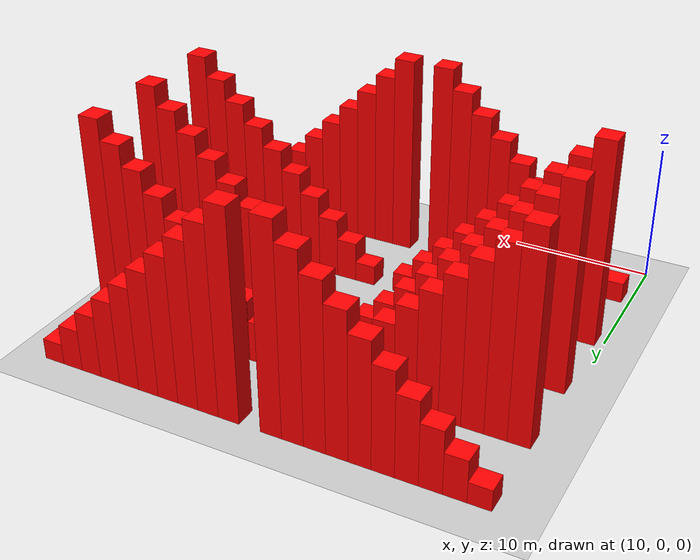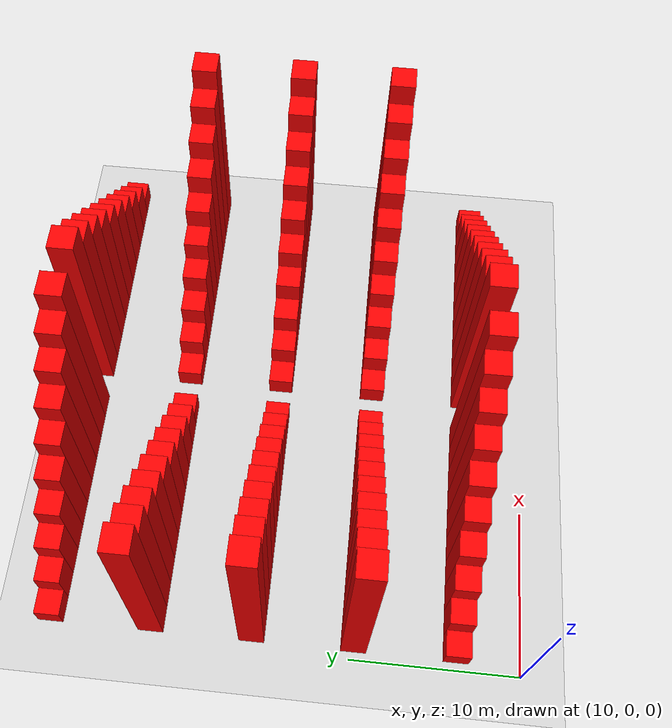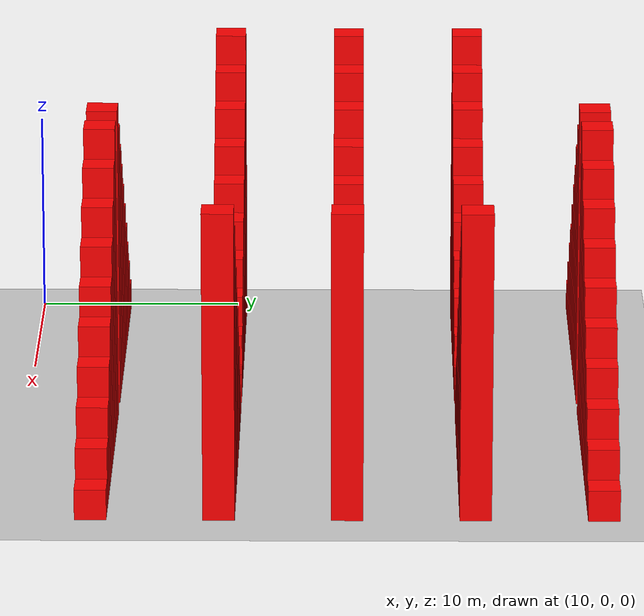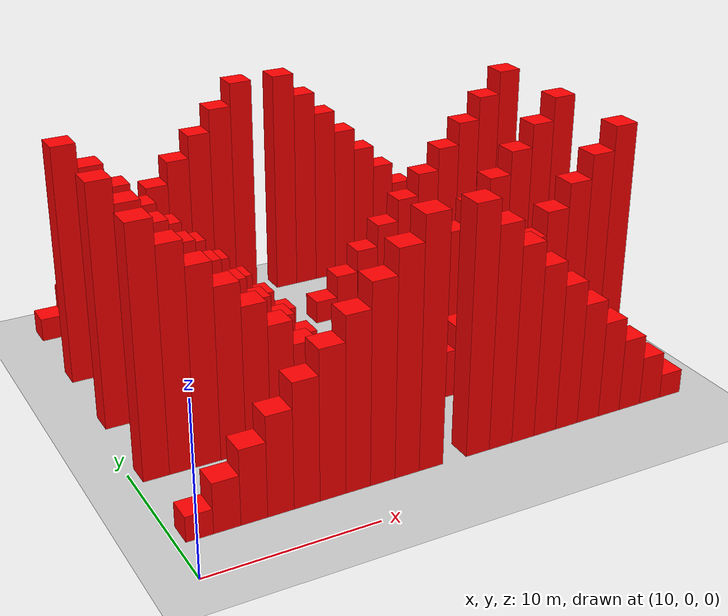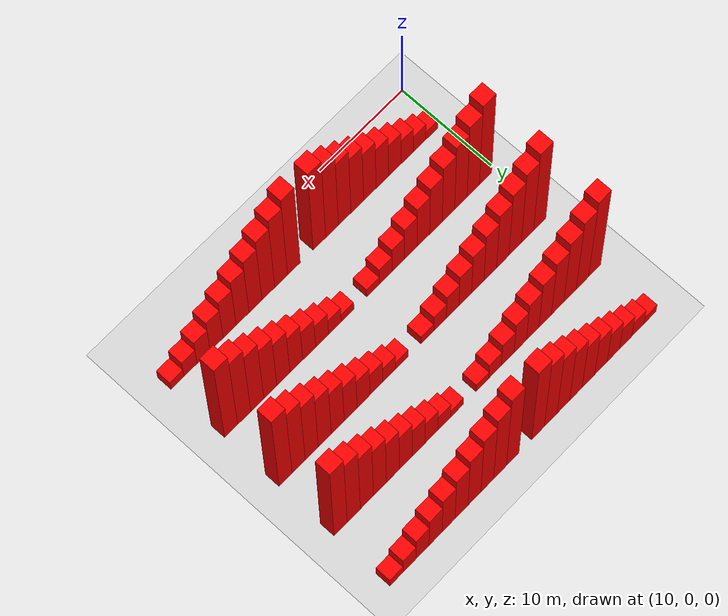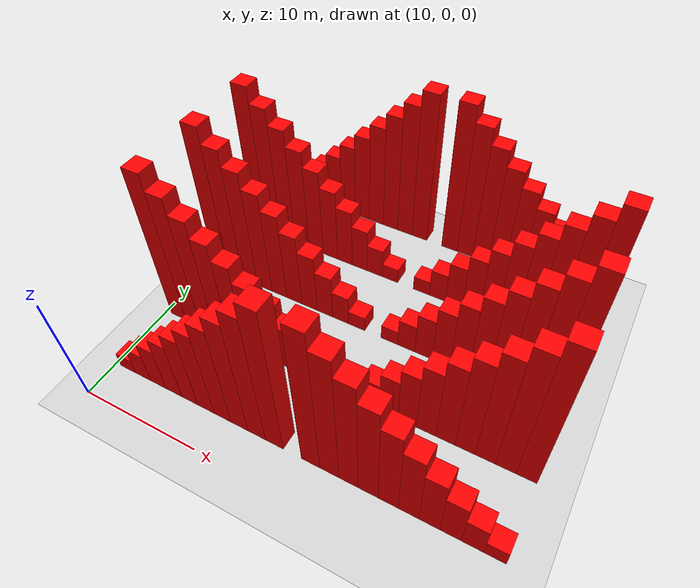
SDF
<sdf version="1.4">
    <world name='default'>
        <!-- A global light source -->
        <include>
            <uri>model://sun</uri>
        </include>
        <!-- A ground plane -->
        <include>
            <uri>model://ground_plane</uri>
        </include>
        <!-- Own physics settings to speed up simulation -->
        <physics type="ode">
            <max_step_size>0.01</max_step_size>
            <real_time_factor>1</real_time_factor>
            <real_time_update_rate>100</real_time_update_rate>
            <gravity>0 0 -9.8</gravity>
        </physics>

                <!-- visual and collisions here-->
 <model name='barrier_7_2_1'>
      <pose> 11.25 3.75 0.75 0 -0 0</pose>
        <static>1</static>
        <link name='link'>
        <collision name='collision'>
          <geometry>
            <box>
              <size>1.5 1.5 1.5</size>
            </box>
          </geometry>
          <max_contacts>10</max_contacts>
          <surface>
            <contact>
              <ode/>
            </contact>
            <bounce/>
            <friction>
              <torsional>
                <ode/>
              </torsional>
              <ode/>
            </friction>
          </surface>
        </collision>
        <visual name='visual'>
          <geometry>
            <box>
              <size>1.5 1.5 1.5</size>
            </box>
          </geometry>
            <material>
              <ambient>1 0 0 1</ambient>
              <diffuse>1 0 0 1</diffuse>
              <specular>0.1 0.1 0.1 1</specular>
              <emissive>0 0 0 0</emissive>
            </material>
        </visual>
        <self_collide>0</self_collide>
        <kinematic>0</kinematic>
        <gravity>1</gravity>
      </link>
    </model>
         <model name='barrier_8_2_2'>
      <pose> 12.75 3.75 1.5 0 -0 0</pose>
        <static>1</static>
        <link name='link'>
        <collision name='collision'>
          <geometry>
            <box>
              <size>1.5 1.5 3.0</size>
            </box>
          </geometry>
          <max_contacts>10</max_contacts>
          <surface>
            <contact>
              <ode/>
            </contact>
            <bounce/>
            <friction>
              <torsional>
                <ode/>
              </torsional>
              <ode/>
            </friction>
          </surface>
        </collision>
        <visual name='visual'>
          <geometry>
            <box>
              <size>1.5 1.5 3.0</size>
            </box>
          </geometry>
            <material>
              <ambient>1 0 0 1</ambient>
              <diffuse>1 0 0 1</diffuse>
              <specular>0.1 0.1 0.1 1</specular>
              <emissive>0 0 0 0</emissive>
            </material>
        </visual>
        <self_collide>0</self_collide>
        <kinematic>0</kinematic>
        <gravity>1</gravity>
      </link>
    </model>
         <model name='barrier_9_2_3'>
      <pose> 14.25 3.75 2.25 0 -0 0</pose>
        <static>1</static>
        <link name='link'>
        <collision name='collision'>
          <geometry>
            <box>
              <size>1.5 1.5 4.5</size>
            </box>
          </geometry>
          <max_contacts>10</max_contacts>
          <surface>
            <contact>
              <ode/>
            </contact>
            <bounce/>
            <friction>
              <torsional>
                <ode/>
              </torsional>
              <ode/>
            </friction>
          </surface>
        </collision>
        <visual name='visual'>
          <geometry>
            <box>
              <size>1.5 1.5 4.5</size>
            </box>
          </geometry>
            <material>
              <ambient>1 0 0 1</ambient>
              <diffuse>1 0 0 1</diffuse>
              <specular>0.1 0.1 0.1 1</specular>
              <emissive>0 0 0 0</emissive>
            </material>
        </visual>
        <self_collide>0</self_collide>
        <kinematic>0</kinematic>
        <gravity>1</gravity>
      </link>
    </model>
         <model name='barrier_10_2_4'>
      <pose> 15.75 3.75 3.0 0 -0 0</pose>
        <static>1</static>
        <link name='link'>
        <collision name='collision'>
          <geometry>
            <box>
              <size>1.5 1.5 6.0</size>
            </box>
          </geometry>
          <max_contacts>10</max_contacts>
          <surface>
            <contact>
              <ode/>
            </contact>
            <bounce/>
            <friction>
              <torsional>
                <ode/>
              </torsional>
              <ode/>
            </friction>
          </surface>
        </collision>
        <visual name='visual'>
          <geometry>
            <box>
              <size>1.5 1.5 6.0</size>
            </box>
          </geometry>
            <material>
              <ambient>1 0 0 1</ambient>
              <diffuse>1 0 0 1</diffuse>
              <specular>0.1 0.1 0.1 1</specular>
              <emissive>0 0 0 0</emissive>
            </material>
        </visual>
        <self_collide>0</self_collide>
        <kinematic>0</kinematic>
        <gravity>1</gravity>
      </link>
    </model>
         <model name='barrier_11_2_5'>
      <pose> 17.25 3.75 3.75 0 -0 0</pose>
        <static>1</static>
        <link name='link'>
        <collision name='collision'>
          <geometry>
            <box>
              <size>1.5 1.5 7.5</size>
            </box>
          </geometry>
          <max_contacts>10</max_contacts>
          <surface>
            <contact>
              <ode/>
            </contact>
            <bounce/>
            <friction>
              <torsional>
                <ode/>
              </torsional>
              <ode/>
            </friction>
          </surface>
        </collision>
        <visual name='visual'>
          <geometry>
            <box>
              <size>1.5 1.5 7.5</size>
            </box>
          </geometry>
            <material>
              <ambient>1 0 0 1</ambient>
              <diffuse>1 0 0 1</diffuse>
              <specular>0.1 0.1 0.1 1</specular>
              <emissive>0 0 0 0</emissive>
            </material>
        </visual>
        <self_collide>0</self_collide>
        <kinematic>0</kinematic>
        <gravity>1</gravity>
      </link>
    </model>
         <model name='barrier_12_2_6'>
      <pose> 18.75 3.75 4.5 0 -0 0</pose>
        <static>1</static>
        <link name='link'>
        <collision name='collision'>
          <geometry>
            <box>
              <size>1.5 1.5 9.0</size>
            </box>
          </geometry>
          <max_contacts>10</max_contacts>
          <surface>
            <contact>
              <ode/>
            </contact>
            <bounce/>
            <friction>
              <torsional>
                <ode/>
              </torsional>
              <ode/>
            </friction>
          </surface>
        </collision>
        <visual name='visual'>
          <geometry>
            <box>
              <size>1.5 1.5 9.0</size>
            </box>
          </geometry>
            <material>
              <ambient>1 0 0 1</ambient>
              <diffuse>1 0 0 1</diffuse>
              <specular>0.1 0.1 0.1 1</specular>
              <emissive>0 0 0 0</emissive>
            </material>
        </visual>
        <self_collide>0</self_collide>
        <kinematic>0</kinematic>
        <gravity>1</gravity>
      </link>
    </model>
         <model name='barrier_13_2_7'>
      <pose> 20.25 3.75 5.25 0 -0 0</pose>
        <static>1</static>
        <link name='link'>
        <collision name='collision'>
          <geometry>
            <box>
              <size>1.5 1.5 10.5</size>
            </box>
          </geometry>
          <max_contacts>10</max_contacts>
          <surface>
            <contact>
              <ode/>
            </contact>
            <bounce/>
            <friction>
              <torsional>
                <ode/>
              </torsional>
              <ode/>
            </friction>
          </surface>
        </collision>
        <visual name='visual'>
          <geometry>
            <box>
              <size>1.5 1.5 10.5</size>
            </box>
          </geometry>
            <material>
              <ambient>1 0 0 1</ambient>
              <diffuse>1 0 0 1</diffuse>
              <specular>0.1 0.1 0.1 1</specular>
              <emissive>0 0 0 0</emissive>
            </material>
        </visual>
        <self_collide>0</self_collide>
        <kinematic>0</kinematic>
        <gravity>1</gravity>
      </link>
    </model>
         <model name='barrier_14_2_8'>
      <pose> 21.75 3.75 6.0 0 -0 0</pose>
        <static>1</static>
        <link name='link'>
        <collision name='collision'>
          <geometry>
            <box>
              <size>1.5 1.5 12.0</size>
            </box>
          </geometry>
          <max_contacts>10</max_contacts>
          <surface>
            <contact>
              <ode/>
            </contact>
            <bounce/>
            <friction>
              <torsional>
                <ode/>
              </torsional>
              <ode/>
            </friction>
          </surface>
        </collision>
        <visual name='visual'>
          <geometry>
            <box>
              <size>1.5 1.5 12.0</size>
            </box>
          </geometry>
            <material>
              <ambient>1 0 0 1</ambient>
              <diffuse>1 0 0 1</diffuse>
              <specular>0.1 0.1 0.1 1</specular>
              <emissive>0 0 0 0</emissive>
            </material>
        </visual>
        <self_collide>0</self_collide>
        <kinematic>0</kinematic>
        <gravity>1</gravity>
      </link>
    </model>
         <model name='barrier_15_2_9'>
      <pose> 23.25 3.75 6.75 0 -0 0</pose>
        <static>1</static>
        <link name='link'>
        <collision name='collision'>
          <geometry>
            <box>
              <size>1.5 1.5 13.5</size>
            </box>
          </geometry>
          <max_contacts>10</max_contacts>
          <surface>
            <contact>
              <ode/>
            </contact>
            <bounce/>
            <friction>
              <torsional>
                <ode/>
              </torsional>
              <ode/>
            </friction>
          </surface>
        </collision>
        <visual name='visual'>
          <geometry>
            <box>
              <size>1.5 1.5 13.5</size>
            </box>
          </geometry>
            <material>
              <ambient>1 0 0 1</ambient>
              <diffuse>1 0 0 1</diffuse>
              <specular>0.1 0.1 0.1 1</specular>
              <emissive>0 0 0 0</emissive>
            </material>
        </visual>
        <self_collide>0</self_collide>
        <kinematic>0</kinematic>
        <gravity>1</gravity>
      </link>
    </model>
         <model name='barrier_16_2_10'>
      <pose> 24.75 3.75 7.5 0 -0 0</pose>
        <static>1</static>
        <link name='link'>
        <collision name='collision'>
          <geometry>
            <box>
              <size>1.5 1.5 15.0</size>
            </box>
          </geometry>
          <max_contacts>10</max_contacts>
          <surface>
            <contact>
              <ode/>
            </contact>
            <bounce/>
            <friction>
              <torsional>
                <ode/>
              </torsional>
              <ode/>
            </friction>
          </surface>
        </collision>
        <visual name='visual'>
          <geometry>
            <box>
              <size>1.5 1.5 15.0</size>
            </box>
          </geometry>
            <material>
              <ambient>1 0 0 1</ambient>
              <diffuse>1 0 0 1</diffuse>
              <specular>0.1 0.1 0.1 1</specular>
              <emissive>0 0 0 0</emissive>
            </material>
        </visual>
        <self_collide>0</self_collide>
        <kinematic>0</kinematic>
        <gravity>1</gravity>
      </link>
    </model>
         <model name='barrier_18_2_10'>
      <pose> 27.75 3.75 7.5 0 -0 0</pose>
        <static>1</static>
        <link name='link'>
        <collision name='collision'>
          <geometry>
            <box>
              <size>1.5 1.5 15.0</size>
            </box>
          </geometry>
          <max_contacts>10</max_contacts>
          <surface>
            <contact>
              <ode/>
            </contact>
            <bounce/>
            <friction>
              <torsional>
                <ode/>
              </torsional>
              <ode/>
            </friction>
          </surface>
        </collision>
        <visual name='visual'>
          <geometry>
            <box>
              <size>1.5 1.5 15.0</size>
            </box>
          </geometry>
            <material>
              <ambient>1 0 0 1</ambient>
              <diffuse>1 0 0 1</diffuse>
              <specular>0.1 0.1 0.1 1</specular>
              <emissive>0 0 0 0</emissive>
            </material>
        </visual>
        <self_collide>0</self_collide>
        <kinematic>0</kinematic>
        <gravity>1</gravity>
      </link>
    </model>
         <model name='barrier_19_2_9'>
      <pose> 29.25 3.75 6.75 0 -0 0</pose>
        <static>1</static>
        <link name='link'>
        <collision name='collision'>
          <geometry>
            <box>
              <size>1.5 1.5 13.5</size>
            </box>
          </geometry>
          <max_contacts>10</max_contacts>
          <surface>
            <contact>
              <ode/>
            </contact>
            <bounce/>
            <friction>
              <torsional>
                <ode/>
              </torsional>
              <ode/>
            </friction>
          </surface>
        </collision>
        <visual name='visual'>
          <geometry>
            <box>
              <size>1.5 1.5 13.5</size>
            </box>
          </geometry>
            <material>
              <ambient>1 0 0 1</ambient>
              <diffuse>1 0 0 1</diffuse>
              <specular>0.1 0.1 0.1 1</specular>
              <emissive>0 0 0 0</emissive>
            </material>
        </visual>
        <self_collide>0</self_collide>
        <kinematic>0</kinematic>
        <gravity>1</gravity>
      </link>
    </model>
         <model name='barrier_20_2_8'>
      <pose> 30.75 3.75 6.0 0 -0 0</pose>
        <static>1</static>
        <link name='link'>
        <collision name='collision'>
          <geometry>
            <box>
              <size>1.5 1.5 12.0</size>
            </box>
          </geometry>
          <max_contacts>10</max_contacts>
          <surface>
            <contact>
              <ode/>
            </contact>
            <bounce/>
            <friction>
              <torsional>
                <ode/>
              </torsional>
              <ode/>
            </friction>
          </surface>
        </collision>
        <visual name='visual'>
          <geometry>
            <box>
              <size>1.5 1.5 12.0</size>
            </box>
          </geometry>
            <material>
              <ambient>1 0 0 1</ambient>
              <diffuse>1 0 0 1</diffuse>
              <specular>0.1 0.1 0.1 1</specular>
              <emissive>0 0 0 0</emissive>
            </material>
        </visual>
        <self_collide>0</self_collide>
        <kinematic>0</kinematic>
        <gravity>1</gravity>
      </link>
    </model>
         <model name='barrier_21_2_7'>
      <pose> 32.25 3.75 5.25 0 -0 0</pose>
        <static>1</static>
        <link name='link'>
        <collision name='collision'>
          <geometry>
            <box>
              <size>1.5 1.5 10.5</size>
            </box>
          </geometry>
          <max_contacts>10</max_contacts>
          <surface>
            <contact>
              <ode/>
            </contact>
            <bounce/>
            <friction>
              <torsional>
                <ode/>
              </torsional>
              <ode/>
            </friction>
          </surface>
        </collision>
        <visual name='visual'>
          <geometry>
            <box>
              <size>1.5 1.5 10.5</size>
            </box>
          </geometry>
            <material>
              <ambient>1 0 0 1</ambient>
              <diffuse>1 0 0 1</diffuse>
              <specular>0.1 0.1 0.1 1</specular>
              <emissive>0 0 0 0</emissive>
            </material>
        </visual>
        <self_collide>0</self_collide>
        <kinematic>0</kinematic>
        <gravity>1</gravity>
      </link>
    </model>
         <model name='barrier_22_2_6'>
      <pose> 33.75 3.75 4.5 0 -0 0</pose>
        <static>1</static>
        <link name='link'>
        <collision name='collision'>
          <geometry>
            <box>
              <size>1.5 1.5 9.0</size>
            </box>
          </geometry>
          <max_contacts>10</max_contacts>
          <surface>
            <contact>
              <ode/>
            </contact>
            <bounce/>
            <friction>
              <torsional>
                <ode/>
              </torsional>
              <ode/>
            </friction>
          </surface>
        </collision>
        <visual name='visual'>
          <geometry>
            <box>
              <size>1.5 1.5 9.0</size>
            </box>
          </geometry>
            <material>
              <ambient>1 0 0 1</ambient>
              <diffuse>1 0 0 1</diffuse>
              <specular>0.1 0.1 0.1 1</specular>
              <emissive>0 0 0 0</emissive>
            </material>
        </visual>
        <self_collide>0</self_collide>
        <kinematic>0</kinematic>
        <gravity>1</gravity>
      </link>
    </model>
         <model name='barrier_23_2_5'>
      <pose> 35.25 3.75 3.75 0 -0 0</pose>
        <static>1</static>
        <link name='link'>
        <collision name='collision'>
          <geometry>
            <box>
              <size>1.5 1.5 7.5</size>
            </box>
          </geometry>
          <max_contacts>10</max_contacts>
          <surface>
            <contact>
              <ode/>
            </contact>
            <bounce/>
            <friction>
              <torsional>
                <ode/>
              </torsional>
              <ode/>
            </friction>
          </surface>
        </collision>
        <visual name='visual'>
          <geometry>
            <box>
              <size>1.5 1.5 7.5</size>
            </box>
          </geometry>
            <material>
              <ambient>1 0 0 1</ambient>
              <diffuse>1 0 0 1</diffuse>
              <specular>0.1 0.1 0.1 1</specular>
              <emissive>0 0 0 0</emissive>
            </material>
        </visual>
        <self_collide>0</self_collide>
        <kinematic>0</kinematic>
        <gravity>1</gravity>
      </link>
    </model>
         <model name='barrier_24_2_4'>
      <pose> 36.75 3.75 3.0 0 -0 0</pose>
        <static>1</static>
        <link name='link'>
        <collision name='collision'>
          <geometry>
            <box>
              <size>1.5 1.5 6.0</size>
            </box>
          </geometry>
          <max_contacts>10</max_contacts>
          <surface>
            <contact>
              <ode/>
            </contact>
            <bounce/>
            <friction>
              <torsional>
                <ode/>
              </torsional>
              <ode/>
            </friction>
          </surface>
        </collision>
        <visual name='visual'>
          <geometry>
            <box>
              <size>1.5 1.5 6.0</size>
            </box>
          </geometry>
            <material>
              <ambient>1 0 0 1</ambient>
              <diffuse>1 0 0 1</diffuse>
              <specular>0.1 0.1 0.1 1</specular>
              <emissive>0 0 0 0</emissive>
            </material>
        </visual>
        <self_collide>0</self_collide>
        <kinematic>0</kinematic>
        <gravity>1</gravity>
      </link>
    </model>
         <model name='barrier_25_2_3'>
      <pose> 38.25 3.75 2.25 0 -0 0</pose>
        <static>1</static>
        <link name='link'>
        <collision name='collision'>
          <geometry>
            <box>
              <size>1.5 1.5 4.5</size>
            </box>
          </geometry>
          <max_contacts>10</max_contacts>
          <surface>
            <contact>
              <ode/>
            </contact>
            <bounce/>
            <friction>
              <torsional>
                <ode/>
              </torsional>
              <ode/>
            </friction>
          </surface>
        </collision>
        <visual name='visual'>
          <geometry>
            <box>
              <size>1.5 1.5 4.5</size>
            </box>
          </geometry>
            <material>
              <ambient>1 0 0 1</ambient>
              <diffuse>1 0 0 1</diffuse>
              <specular>0.1 0.1 0.1 1</specular>
              <emissive>0 0 0 0</emissive>
            </material>
        </visual>
        <self_collide>0</self_collide>
        <kinematic>0</kinematic>
        <gravity>1</gravity>
      </link>
    </model>
         <model name='barrier_26_2_2'>
      <pose> 39.75 3.75 1.5 0 -0 0</pose>
        <static>1</static>
        <link name='link'>
        <collision name='collision'>
          <geometry>
            <box>
              <size>1.5 1.5 3.0</size>
            </box>
          </geometry>
          <max_contacts>10</max_contacts>
          <surface>
            <contact>
              <ode/>
            </contact>
            <bounce/>
            <friction>
              <torsional>
                <ode/>
              </torsional>
              <ode/>
            </friction>
          </surface>
        </collision>
        <visual name='visual'>
          <geometry>
            <box>
              <size>1.5 1.5 3.0</size>
            </box>
          </geometry>
            <material>
              <ambient>1 0 0 1</ambient>
              <diffuse>1 0 0 1</diffuse>
              <specular>0.1 0.1 0.1 1</specular>
              <emissive>0 0 0 0</emissive>
            </material>
        </visual>
        <self_collide>0</self_collide>
        <kinematic>0</kinematic>
        <gravity>1</gravity>
      </link>
    </model>
         <model name='barrier_27_2_1'>
      <pose> 41.25 3.75 0.75 0 -0 0</pose>
        <static>1</static>
        <link name='link'>
        <collision name='collision'>
          <geometry>
            <box>
              <size>1.5 1.5 1.5</size>
            </box>
          </geometry>
          <max_contacts>10</max_contacts>
          <surface>
            <contact>
              <ode/>
            </contact>
            <bounce/>
            <friction>
              <torsional>
                <ode/>
              </torsional>
              <ode/>
            </friction>
          </surface>
        </collision>
        <visual name='visual'>
          <geometry>
            <box>
              <size>1.5 1.5 1.5</size>
            </box>
          </geometry>
            <material>
              <ambient>1 0 0 1</ambient>
              <diffuse>1 0 0 1</diffuse>
              <specular>0.1 0.1 0.1 1</specular>
              <emissive>0 0 0 0</emissive>
            </material>
        </visual>
        <self_collide>0</self_collide>
        <kinematic>0</kinematic>
        <gravity>1</gravity>
      </link>
    </model>
         <model name='barrier_7_6_10'>
      <pose> 11.25 9.75 7.5 0 -0 0</pose>
        <static>1</static>
        <link name='link'>
        <collision name='collision'>
          <geometry>
            <box>
              <size>1.5 1.5 15.0</size>
            </box>
          </geometry>
          <max_contacts>10</max_contacts>
          <surface>
            <contact>
              <ode/>
            </contact>
            <bounce/>
            <friction>
              <torsional>
                <ode/>
              </torsional>
              <ode/>
            </friction>
          </surface>
        </collision>
        <visual name='visual'>
          <geometry>
            <box>
              <size>1.5 1.5 15.0</size>
            </box>
          </geometry>
            <material>
              <ambient>1 0 0 1</ambient>
              <diffuse>1 0 0 1</diffuse>
              <specular>0.1 0.1 0.1 1</specular>
              <emissive>0 0 0 0</emissive>
            </material>
        </visual>
        <self_collide>0</self_collide>
        <kinematic>0</kinematic>
        <gravity>1</gravity>
      </link>
    </model>
         <model name='barrier_8_6_9'>
      <pose> 12.75 9.75 6.75 0 -0 0</pose>
        <static>1</static>
        <link name='link'>
        <collision name='collision'>
          <geometry>
            <box>
              <size>1.5 1.5 13.5</size>
            </box>
          </geometry>
          <max_contacts>10</max_contacts>
          <surface>
            <contact>
              <ode/>
            </contact>
            <bounce/>
            <friction>
              <torsional>
                <ode/>
              </torsional>
              <ode/>
            </friction>
          </surface>
        </collision>
        <visual name='visual'>
          <geometry>
            <box>
              <size>1.5 1.5 13.5</size>
            </box>
          </geometry>
            <material>
              <ambient>1 0 0 1</ambient>
              <diffuse>1 0 0 1</diffuse>
              <specular>0.1 0.1 0.1 1</specular>
              <emissive>0 0 0 0</emissive>
            </material>
        </visual>
        <self_collide>0</self_collide>
        <kinematic>0</kinematic>
        <gravity>1</gravity>
      </link>
    </model>
         <model name='barrier_9_6_8'>
      <pose> 14.25 9.75 6.0 0 -0 0</pose>
        <static>1</static>
        <link name='link'>
        <collision name='collision'>
          <geometry>
            <box>
              <size>1.5 1.5 12.0</size>
            </box>
          </geometry>
          <max_contacts>10</max_contacts>
          <surface>
            <contact>
              <ode/>
            </contact>
            <bounce/>
            <friction>
              <torsional>
                <ode/>
              </torsional>
              <ode/>
            </friction>
          </surface>
        </collision>
        <visual name='visual'>
          <geometry>
            <box>
              <size>1.5 1.5 12.0</size>
            </box>
          </geometry>
            <material>
              <ambient>1 0 0 1</ambient>
              <diffuse>1 0 0 1</diffuse>
              <specular>0.1 0.1 0.1 1</specular>
              <emissive>0 0 0 0</emissive>
            </material>
        </visual>
        <self_collide>0</self_collide>
        <kinematic>0</kinematic>
        <gravity>1</gravity>
      </link>
    </model>
         <model name='barrier_10_6_7'>
      <pose> 15.75 9.75 5.25 0 -0 0</pose>
        <static>1</static>
        <link name='link'>
        <collision name='collision'>
          <geometry>
            <box>
              <size>1.5 1.5 10.5</size>
            </box>
          </geometry>
          <max_contacts>10</max_contacts>
          <surface>
            <contact>
              <ode/>
            </contact>
            <bounce/>
            <friction>
              <torsional>
                <ode/>
              </torsional>
              <ode/>
            </friction>
          </surface>
        </collision>
        <visual name='visual'>
          <geometry>
            <box>
              <size>1.5 1.5 10.5</size>
            </box>
          </geometry>
            <material>
              <ambient>1 0 0 1</ambient>
              <diffuse>1 0 0 1</diffuse>
              <specular>0.1 0.1 0.1 1</specular>
              <emissive>0 0 0 0</emissive>
            </material>
        </visual>
        <self_collide>0</self_collide>
        <kinematic>0</kinematic>
        <gravity>1</gravity>
      </link>
    </model>
         <model name='barrier_11_6_6'>
      <pose> 17.25 9.75 4.5 0 -0 0</pose>
        <static>1</static>
        <link name='link'>
        <collision name='collision'>
          <geometry>
            <box>
              <size>1.5 1.5 9.0</size>
            </box>
          </geometry>
          <max_contacts>10</max_contacts>
          <surface>
            <contact>
              <ode/>
            </contact>
            <bounce/>
            <friction>
              <torsional>
                <ode/>
              </torsional>
              <ode/>
            </friction>
          </surface>
        </collision>
        <visual name='visual'>
          <geometry>
            <box>
              <size>1.5 1.5 9.0</size>
            </box>
          </geometry>
            <material>
              <ambient>1 0 0 1</ambient>
              <diffuse>1 0 0 1</diffuse>
              <specular>0.1 0.1 0.1 1</specular>
              <emissive>0 0 0 0</emissive>
            </material>
        </visual>
        <self_collide>0</self_collide>
        <kinematic>0</kinematic>
        <gravity>1</gravity>
      </link>
    </model>
         <model name='barrier_12_6_5'>
      <pose> 18.75 9.75 3.75 0 -0 0</pose>
        <static>1</static>
        <link name='link'>
        <collision name='collision'>
          <geometry>
            <box>
              <size>1.5 1.5 7.5</size>
            </box>
          </geometry>
          <max_contacts>10</max_contacts>
          <surface>
            <contact>
              <ode/>
            </contact>
            <bounce/>
            <friction>
              <torsional>
                <ode/>
              </torsional>
              <ode/>
            </friction>
          </surface>
        </collision>
        <visual name='visual'>
          <geometry>
            <box>
              <size>1.5 1.5 7.5</size>
            </box>
          </geometry>
            <material>
              <ambient>1 0 0 1</ambient>
              <diffuse>1 0 0 1</diffuse>
              <specular>0.1 0.1 0.1 1</specular>
              <emissive>0 0 0 0</emissive>
            </material>
        </visual>
        <self_collide>0</self_collide>
        <kinematic>0</kinematic>
        <gravity>1</gravity>
      </link>
    </model>
         <model name='barrier_13_6_4'>
      <pose> 20.25 9.75 3.0 0 -0 0</pose>
        <static>1</static>
        <link name='link'>
        <collision name='collision'>
          <geometry>
            <box>
              <size>1.5 1.5 6.0</size>
            </box>
          </geometry>
          <max_contacts>10</max_contacts>
          <surface>
            <contact>
              <ode/>
            </contact>
            <bounce/>
            <friction>
              <torsional>
                <ode/>
              </torsional>
              <ode/>
            </friction>
          </surface>
        </collision>
        <visual name='visual'>
          <geometry>
            <box>
              <size>1.5 1.5 6.0</size>
            </box>
          </geometry>
            <material>
              <ambient>1 0 0 1</ambient>
              <diffuse>1 0 0 1</diffuse>
              <specular>0.1 0.1 0.1 1</specular>
              <emissive>0 0 0 0</emissive>
            </material>
        </visual>
        <self_collide>0</self_collide>
        <kinematic>0</kinematic>
        <gravity>1</gravity>
      </link>
    </model>
         <model name='barrier_14_6_3'>
      <pose> 21.75 9.75 2.25 0 -0 0</pose>
        <static>1</static>
        <link name='link'>
        <collision name='collision'>
          <geometry>
            <box>
              <size>1.5 1.5 4.5</size>
            </box>
          </geometry>
          <max_contacts>10</max_contacts>
          <surface>
            <contact>
              <ode/>
            </contact>
            <bounce/>
            <friction>
              <torsional>
                <ode/>
              </torsional>
              <ode/>
            </friction>
          </surface>
        </collision>
        <visual name='visual'>
          <geometry>
            <box>
              <size>1.5 1.5 4.5</size>
            </box>
          </geometry>
            <material>
              <ambient>1 0 0 1</ambient>
              <diffuse>1 0 0 1</diffuse>
              <specular>0.1 0.1 0.1 1</specular>
              <emissive>0 0 0 0</emissive>
            </material>
        </visual>
        <self_collide>0</self_collide>
        <kinematic>0</kinematic>
        <gravity>1</gravity>
      </link>
    </model>
         <model name='barrier_15_6_2'>
      <pose> 23.25 9.75 1.5 0 -0 0</pose>
        <static>1</static>
        <link name='link'>
        <collision name='collision'>
          <geometry>
            <box>
              <size>1.5 1.5 3.0</size>
            </box>
          </geometry>
          <max_contacts>10</max_contacts>
          <surface>
            <contact>
              <ode/>
            </contact>
            <bounce/>
            <friction>
              <torsional>
                <ode/>
              </torsional>
              <ode/>
            </friction>
          </surface>
        </collision>
        <visual name='visual'>
          <geometry>
            <box>
              <size>1.5 1.5 3.0</size>
            </box>
          </geometry>
            <material>
              <ambient>1 0 0 1</ambient>
              <diffuse>1 0 0 1</diffuse>
              <specular>0.1 0.1 0.1 1</specular>
              <emissive>0 0 0 0</emissive>
            </material>
        </visual>
        <self_collide>0</self_collide>
        <kinematic>0</kinematic>
        <gravity>1</gravity>
      </link>
    </model>
         <model name='barrier_16_6_1'>
      <pose> 24.75 9.75 0.75 0 -0 0</pose>
        <static>1</static>
        <link name='link'>
        <collision name='collision'>
          <geometry>
            <box>
              <size>1.5 1.5 1.5</size>
            </box>
          </geometry>
          <max_contacts>10</max_contacts>
          <surface>
            <contact>
              <ode/>
            </contact>
            <bounce/>
            <friction>
              <torsional>
                <ode/>
              </torsional>
              <ode/>
            </friction>
          </surface>
        </collision>
        <visual name='visual'>
          <geometry>
            <box>
              <size>1.5 1.5 1.5</size>
            </box>
          </geometry>
            <material>
              <ambient>1 0 0 1</ambient>
              <diffuse>1 0 0 1</diffuse>
              <specular>0.1 0.1 0.1 1</specular>
              <emissive>0 0 0 0</emissive>
            </material>
        </visual>
        <self_collide>0</self_collide>
        <kinematic>0</kinematic>
        <gravity>1</gravity>
      </link>
    </model>
         <model name='barrier_18_6_1'>
      <pose> 27.75 9.75 0.75 0 -0 0</pose>
        <static>1</static>
        <link name='link'>
        <collision name='collision'>
          <geometry>
            <box>
              <size>1.5 1.5 1.5</size>
            </box>
          </geometry>
          <max_contacts>10</max_contacts>
          <surface>
            <contact>
              <ode/>
            </contact>
            <bounce/>
            <friction>
              <torsional>
                <ode/>
              </torsional>
              <ode/>
            </friction>
          </surface>
        </collision>
        <visual name='visual'>
          <geometry>
            <box>
              <size>1.5 1.5 1.5</size>
            </box>
          </geometry>
            <material>
              <ambient>1 0 0 1</ambient>
              <diffuse>1 0 0 1</diffuse>
              <specular>0.1 0.1 0.1 1</specular>
              <emissive>0 0 0 0</emissive>
            </material>
        </visual>
        <self_collide>0</self_collide>
        <kinematic>0</kinematic>
        <gravity>1</gravity>
      </link>
    </model>
         <model name='barrier_19_6_2'>
      <pose> 29.25 9.75 1.5 0 -0 0</pose>
        <static>1</static>
        <link name='link'>
        <collision name='collision'>
          <geometry>
            <box>
              <size>1.5 1.5 3.0</size>
            </box>
          </geometry>
          <max_contacts>10</max_contacts>
          <surface>
            <contact>
              <ode/>
            </contact>
            <bounce/>
            <friction>
              <torsional>
                <ode/>
              </torsional>
              <ode/>
            </friction>
          </surface>
        </collision>
        <visual name='visual'>
          <geometry>
            <box>
              <size>1.5 1.5 3.0</size>
            </box>
          </geometry>
            <material>
              <ambient>1 0 0 1</ambient>
              <diffuse>1 0 0 1</diffuse>
              <specular>0.1 0.1 0.1 1</specular>
              <emissive>0 0 0 0</emissive>
            </material>
        </visual>
        <self_collide>0</self_collide>
        <kinematic>0</kinematic>
        <gravity>1</gravity>
      </link>
    </model>
         <model name='barrier_20_6_3'>
      <pose> 30.75 9.75 2.25 0 -0 0</pose>
        <static>1</static>
        <link name='link'>
        <collision name='collision'>
          <geometry>
            <box>
              <size>1.5 1.5 4.5</size>
            </box>
          </geometry>
          <max_contacts>10</max_contacts>
          <surface>
            <contact>
              <ode/>
            </contact>
            <bounce/>
            <friction>
              <torsional>
                <ode/>
              </torsional>
              <ode/>
            </friction>
          </surface>
        </collision>
        <visual name='visual'>
          <geometry>
            <box>
              <size>1.5 1.5 4.5</size>
            </box>
          </geometry>
            <material>
              <ambient>1 0 0 1</ambient>
              <diffuse>1 0 0 1</diffuse>
              <specular>0.1 0.1 0.1 1</specular>
              <emissive>0 0 0 0</emissive>
            </material>
        </visual>
        <self_collide>0</self_collide>
        <kinematic>0</kinematic>
        <gravity>1</gravity>
      </link>
    </model>
         <model name='barrier_21_6_4'>
      <pose> 32.25 9.75 3.0 0 -0 0</pose>
        <static>1</static>
        <link name='link'>
        <collision name='collision'>
          <geometry>
            <box>
              <size>1.5 1.5 6.0</size>
            </box>
          </geometry>
          <max_contacts>10</max_contacts>
          <surface>
            <contact>
              <ode/>
            </contact>
            <bounce/>
            <friction>
              <torsional>
                <ode/>
              </torsional>
              <ode/>
            </friction>
          </surface>
        </collision>
        <visual name='visual'>
          <geometry>
            <box>
              <size>1.5 1.5 6.0</size>
            </box>
          </geometry>
            <material>
              <ambient>1 0 0 1</ambient>
              <diffuse>1 0 0 1</diffuse>
              <specular>0.1 0.1 0.1 1</specular>
              <emissive>0 0 0 0</emissive>
            </material>
        </visual>
        <self_collide>0</self_collide>
        <kinematic>0</kinematic>
        <gravity>1</gravity>
      </link>
    </model>
         <model name='barrier_22_6_5'>
      <pose> 33.75 9.75 3.75 0 -0 0</pose>
        <static>1</static>
        <link name='link'>
        <collision name='collision'>
          <geometry>
            <box>
              <size>1.5 1.5 7.5</size>
            </box>
          </geometry>
          <max_contacts>10</max_contacts>
          <surface>
            <contact>
              <ode/>
            </contact>
            <bounce/>
            <friction>
              <torsional>
                <ode/>
              </torsional>
              <ode/>
            </friction>
          </surface>
        </collision>
        <visual name='visual'>
          <geometry>
            <box>
              <size>1.5 1.5 7.5</size>
            </box>
          </geometry>
            <material>
              <ambient>1 0 0 1</ambient>
              <diffuse>1 0 0 1</diffuse>
              <specular>0.1 0.1 0.1 1</specular>
              <emissive>0 0 0 0</emissive>
            </material>
        </visual>
        <self_collide>0</self_collide>
        <kinematic>0</kinematic>
        <gravity>1</gravity>
      </link>
    </model>
         <model name='barrier_23_6_6'>
      <pose> 35.25 9.75 4.5 0 -0 0</pose>
        <static>1</static>
        <link name='link'>
        <collision name='collision'>
          <geometry>
            <box>
              <size>1.5 1.5 9.0</size>
            </box>
          </geometry>
          <max_contacts>10</max_contacts>
          <surface>
            <contact>
              <ode/>
            </contact>
            <bounce/>
            <friction>
              <torsional>
                <ode/>
              </torsional>
              <ode/>
            </friction>
          </surface>
        </collision>
        <visual name='visual'>
          <geometry>
            <box>
              <size>1.5 1.5 9.0</size>
            </box>
          </geometry>
            <material>
              <ambient>1 0 0 1</ambient>
              <diffuse>1 0 0 1</diffuse>
              <specular>0.1 0.1 0.1 1</specular>
              <emissive>0 0 0 0</emissive>
            </material>
        </visual>
        <self_collide>0</self_collide>
        <kinematic>0</kinematic>
        <gravity>1</gravity>
      </link>
    </model>
         <model name='barrier_24_6_7'>
      <pose> 36.75 9.75 5.25 0 -0 0</pose>
        <static>1</static>
        <link name='link'>
        <collision name='collision'>
          <geometry>
            <box>
              <size>1.5 1.5 10.5</size>
            </box>
          </geometry>
          <max_contacts>10</max_contacts>
          <surface>
            <contact>
              <ode/>
            </contact>
            <bounce/>
            <friction>
              <torsional>
                <ode/>
              </torsional>
              <ode/>
            </friction>
          </surface>
        </collision>
        <visual name='visual'>
          <geometry>
            <box>
              <size>1.5 1.5 10.5</size>
            </box>
          </geometry>
            <material>
              <ambient>1 0 0 1</ambient>
              <diffuse>1 0 0 1</diffuse>
              <specular>0.1 0.1 0.1 1</specular>
              <emissive>0 0 0 0</emissive>
            </material>
        </visual>
        <self_collide>0</self_collide>
        <kinematic>0</kinematic>
        <gravity>1</gravity>
      </link>
    </model>
         <model name='barrier_25_6_8'>
      <pose> 38.25 9.75 6.0 0 -0 0</pose>
        <static>1</static>
        <link name='link'>
        <collision name='collision'>
          <geometry>
            <box>
              <size>1.5 1.5 12.0</size>
            </box>
          </geometry>
          <max_contacts>10</max_contacts>
          <surface>
            <contact>
              <ode/>
            </contact>
            <bounce/>
            <friction>
              <torsional>
                <ode/>
              </torsional>
              <ode/>
            </friction>
          </surface>
        </collision>
        <visual name='visual'>
          <geometry>
            <box>
              <size>1.5 1.5 12.0</size>
            </box>
          </geometry>
            <material>
              <ambient>1 0 0 1</ambient>
              <diffuse>1 0 0 1</diffuse>
              <specular>0.1 0.1 0.1 1</specular>
              <emissive>0 0 0 0</emissive>
            </material>
        </visual>
        <self_collide>0</self_collide>
        <kinematic>0</kinematic>
        <gravity>1</gravity>
      </link>
    </model>
         <model name='barrier_26_6_9'>
      <pose> 39.75 9.75 6.75 0 -0 0</pose>
        <static>1</static>
        <link name='link'>
        <collision name='collision'>
          <geometry>
            <box>
              <size>1.5 1.5 13.5</size>
            </box>
          </geometry>
          <max_contacts>10</max_contacts>
          <surface>
            <contact>
              <ode/>
            </contact>
            <bounce/>
            <friction>
              <torsional>
                <ode/>
              </torsional>
              <ode/>
            </friction>
          </surface>
        </collision>
        <visual name='visual'>
          <geometry>
            <box>
              <size>1.5 1.5 13.5</size>
            </box>
          </geometry>
            <material>
              <ambient>1 0 0 1</ambient>
              <diffuse>1 0 0 1</diffuse>
              <specular>0.1 0.1 0.1 1</specular>
              <emissive>0 0 0 0</emissive>
            </material>
        </visual>
        <self_collide>0</self_collide>
        <kinematic>0</kinematic>
        <gravity>1</gravity>
      </link>
    </model>
         <model name='barrier_27_6_10'>
      <pose> 41.25 9.75 7.5 0 -0 0</pose>
        <static>1</static>
        <link name='link'>
        <collision name='collision'>
          <geometry>
            <box>
              <size>1.5 1.5 15.0</size>
            </box>
          </geometry>
          <max_contacts>10</max_contacts>
          <surface>
            <contact>
              <ode/>
            </contact>
            <bounce/>
            <friction>
              <torsional>
                <ode/>
              </torsional>
              <ode/>
            </friction>
          </surface>
        </collision>
        <visual name='visual'>
          <geometry>
            <box>
              <size>1.5 1.5 15.0</size>
            </box>
          </geometry>
            <material>
              <ambient>1 0 0 1</ambient>
              <diffuse>1 0 0 1</diffuse>
              <specular>0.1 0.1 0.1 1</specular>
              <emissive>0 0 0 0</emissive>
            </material>
        </visual>
        <self_collide>0</self_collide>
        <kinematic>0</kinematic>
        <gravity>1</gravity>
      </link>
    </model>
         <model name='barrier_7_10_10'>
      <pose> 11.25 15.75 7.5 0 -0 0</pose>
        <static>1</static>
        <link name='link'>
        <collision name='collision'>
          <geometry>
            <box>
              <size>1.5 1.5 15.0</size>
            </box>
          </geometry>
          <max_contacts>10</max_contacts>
          <surface>
            <contact>
              <ode/>
            </contact>
            <bounce/>
            <friction>
              <torsional>
                <ode/>
              </torsional>
              <ode/>
            </friction>
          </surface>
        </collision>
        <visual name='visual'>
          <geometry>
            <box>
              <size>1.5 1.5 15.0</size>
            </box>
          </geometry>
            <material>
              <ambient>1 0 0 1</ambient>
              <diffuse>1 0 0 1</diffuse>
              <specular>0.1 0.1 0.1 1</specular>
              <emissive>0 0 0 0</emissive>
            </material>
        </visual>
        <self_collide>0</self_collide>
        <kinematic>0</kinematic>
        <gravity>1</gravity>
      </link>
    </model>
         <model name='barrier_8_10_9'>
      <pose> 12.75 15.75 6.75 0 -0 0</pose>
        <static>1</static>
        <link name='link'>
        <collision name='collision'>
          <geometry>
            <box>
              <size>1.5 1.5 13.5</size>
            </box>
          </geometry>
          <max_contacts>10</max_contacts>
          <surface>
            <contact>
              <ode/>
            </contact>
            <bounce/>
            <friction>
              <torsional>
                <ode/>
              </torsional>
              <ode/>
            </friction>
          </surface>
        </collision>
        <visual name='visual'>
          <geometry>
            <box>
              <size>1.5 1.5 13.5</size>
            </box>
          </geometry>
            <material>
              <ambient>1 0 0 1</ambient>
              <diffuse>1 0 0 1</diffuse>
              <specular>0.1 0.1 0.1 1</specular>
              <emissive>0 0 0 0</emissive>
            </material>
        </visual>
        <self_collide>0</self_collide>
        <kinematic>0</kinematic>
        <gravity>1</gravity>
      </link>
    </model>
         <model name='barrier_9_10_8'>
      <pose> 14.25 15.75 6.0 0 -0 0</pose>
        <static>1</static>
        <link name='link'>
        <collision name='collision'>
          <geometry>
            <box>
              <size>1.5 1.5 12.0</size>
            </box>
          </geometry>
          <max_contacts>10</max_contacts>
          <surface>
            <contact>
              <ode/>
            </contact>
            <bounce/>
            <friction>
              <torsional>
                <ode/>
              </torsional>
              <ode/>
            </friction>
          </surface>
        </collision>
        <visual name='visual'>
          <geometry>
            <box>
              <size>1.5 1.5 12.0</size>
            </box>
          </geometry>
            <material>
              <ambient>1 0 0 1</ambient>
              <diffuse>1 0 0 1</diffuse>
              <specular>0.1 0.1 0.1 1</specular>
              <emissive>0 0 0 0</emissive>
            </material>
        </visual>
        <self_collide>0</self_collide>
        <kinematic>0</kinematic>
        <gravity>1</gravity>
      </link>
    </model>
         <model name='barrier_10_10_7'>
      <pose> 15.75 15.75 5.25 0 -0 0</pose>
        <static>1</static>
        <link name='link'>
        <collision name='collision'>
          <geometry>
            <box>
              <size>1.5 1.5 10.5</size>
            </box>
          </geometry>
          <max_contacts>10</max_contacts>
          <surface>
            <contact>
              <ode/>
            </contact>
            <bounce/>
            <friction>
              <torsional>
                <ode/>
              </torsional>
              <ode/>
            </friction>
          </surface>
        </collision>
        <visual name='visual'>
          <geometry>
            <box>
              <size>1.5 1.5 10.5</size>
            </box>
          </geometry>
            <material>
              <ambient>1 0 0 1</ambient>
              <diffuse>1 0 0 1</diffuse>
              <specular>0.1 0.1 0.1 1</specular>
              <emissive>0 0 0 0</emissive>
            </material>
        </visual>
        <self_collide>0</self_collide>
        <kinematic>0</kinematic>
        <gravity>1</gravity>
      </link>
    </model>
         <model name='barrier_11_10_6'>
      <pose> 17.25 15.75 4.5 0 -0 0</pose>
        <static>1</static>
        <link name='link'>
        <collision name='collision'>
          <geometry>
            <box>
              <size>1.5 1.5 9.0</size>
            </box>
          </geometry>
          <max_contacts>10</max_contacts>
          <surface>
            <contact>
              <ode/>
            </contact>
            <bounce/>
            <friction>
              <torsional>
                <ode/>
              </torsional>
              <ode/>
            </friction>
          </surface>
        </collision>
        <visual name='visual'>
          <geometry>
            <box>
              <size>1.5 1.5 9.0</size>
            </box>
          </geometry>
            <material>
              <ambient>1 0 0 1</ambient>
              <diffuse>1 0 0 1</diffuse>
              <specular>0.1 0.1 0.1 1</specular>
              <emissive>0 0 0 0</emissive>
            </material>
        </visual>
        <self_collide>0</self_collide>
        <kinematic>0</kinematic>
        <gravity>1</gravity>
      </link>
    </model>
         <model name='barrier_12_10_5'>
      <pose> 18.75 15.75 3.75 0 -0 0</pose>
        <static>1</static>
        <link name='link'>
        <collision name='collision'>
          <geometry>
            <box>
              <size>1.5 1.5 7.5</size>
            </box>
          </geometry>
          <max_contacts>10</max_contacts>
          <surface>
            <contact>
              <ode/>
            </contact>
            <bounce/>
            <friction>
              <torsional>
                <ode/>
              </torsional>
              <ode/>
            </friction>
          </surface>
        </collision>
        <visual name='visual'>
          <geometry>
            <box>
              <size>1.5 1.5 7.5</size>
            </box>
          </geometry>
            <material>
              <ambient>1 0 0 1</ambient>
              <diffuse>1 0 0 1</diffuse>
              <specular>0.1 0.1 0.1 1</specular>
              <emissive>0 0 0 0</emissive>
            </material>
        </visual>
        <self_collide>0</self_collide>
        <kinematic>0</kinematic>
        <gravity>1</gravity>
      </link>
    </model>
         <model name='barrier_13_10_4'>
      <pose> 20.25 15.75 3.0 0 -0 0</pose>
        <static>1</static>
        <link name='link'>
        <collision name='collision'>
          <geometry>
            <box>
              <size>1.5 1.5 6.0</size>
            </box>
          </geometry>
          <max_contacts>10</max_contacts>
          <surface>
            <contact>
              <ode/>
            </contact>
            <bounce/>
            <friction>
              <torsional>
                <ode/>
              </torsional>
              <ode/>
            </friction>
          </surface>
        </collision>
        <visual name='visual'>
          <geometry>
            <box>
              <size>1.5 1.5 6.0</size>
            </box>
          </geometry>
            <material>
              <ambient>1 0 0 1</ambient>
              <diffuse>1 0 0 1</diffuse>
              <specular>0.1 0.1 0.1 1</specular>
              <emissive>0 0 0 0</emissive>
            </material>
        </visual>
        <self_collide>0</self_collide>
        <kinematic>0</kinematic>
        <gravity>1</gravity>
      </link>
    </model>
         <model name='barrier_14_10_3'>
      <pose> 21.75 15.75 2.25 0 -0 0</pose>
        <static>1</static>
        <link name='link'>
        <collision name='collision'>
          <geometry>
            <box>
              <size>1.5 1.5 4.5</size>
            </box>
          </geometry>
          <max_contacts>10</max_contacts>
          <surface>
            <contact>
              <ode/>
            </contact>
            <bounce/>
            <friction>
              <torsional>
                <ode/>
              </torsional>
              <ode/>
            </friction>
          </surface>
        </collision>
        <visual name='visual'>
          <geometry>
            <box>
              <size>1.5 1.5 4.5</size>
            </box>
          </geometry>
            <material>
              <ambient>1 0 0 1</ambient>
              <diffuse>1 0 0 1</diffuse>
              <specular>0.1 0.1 0.1 1</specular>
              <emissive>0 0 0 0</emissive>
            </material>
        </visual>
        <self_collide>0</self_collide>
        <kinematic>0</kinematic>
        <gravity>1</gravity>
      </link>
    </model>
         <model name='barrier_15_10_2'>
      <pose> 23.25 15.75 1.5 0 -0 0</pose>
        <static>1</static>
        <link name='link'>
        <collision name='collision'>
          <geometry>
            <box>
              <size>1.5 1.5 3.0</size>
            </box>
          </geometry>
          <max_contacts>10</max_contacts>
          <surface>
            <contact>
              <ode/>
            </contact>
            <bounce/>
            <friction>
              <torsional>
                <ode/>
              </torsional>
              <ode/>
            </friction>
          </surface>
        </collision>
        <visual name='visual'>
          <geometry>
            <box>
              <size>1.5 1.5 3.0</size>
            </box>
          </geometry>
            <material>
              <ambient>1 0 0 1</ambient>
              <diffuse>1 0 0 1</diffuse>
              <specular>0.1 0.1 0.1 1</specular>
              <emissive>0 0 0 0</emissive>
            </material>
        </visual>
        <self_collide>0</self_collide>
        <kinematic>0</kinematic>
        <gravity>1</gravity>
      </link>
    </model>
         <model name='barrier_16_10_1'>
      <pose> 24.75 15.75 0.75 0 -0 0</pose>
        <static>1</static>
        <link name='link'>
        <collision name='collision'>
          <geometry>
            <box>
              <size>1.5 1.5 1.5</size>
            </box>
          </geometry>
          <max_contacts>10</max_contacts>
          <surface>
            <contact>
              <ode/>
            </contact>
            <bounce/>
            <friction>
              <torsional>
                <ode/>
              </torsional>
              <ode/>
            </friction>
          </surface>
        </collision>
        <visual name='visual'>
          <geometry>
            <box>
              <size>1.5 1.5 1.5</size>
            </box>
          </geometry>
            <material>
              <ambient>1 0 0 1</ambient>
              <diffuse>1 0 0 1</diffuse>
              <specular>0.1 0.1 0.1 1</specular>
              <emissive>0 0 0 0</emissive>
            </material>
        </visual>
        <self_collide>0</self_collide>
        <kinematic>0</kinematic>
        <gravity>1</gravity>
      </link>
    </model>
         <model name='barrier_18_10_1'>
      <pose> 27.75 15.75 0.75 0 -0 0</pose>
        <static>1</static>
        <link name='link'>
        <collision name='collision'>
          <geometry>
            <box>
              <size>1.5 1.5 1.5</size>
            </box>
          </geometry>
          <max_contacts>10</max_contacts>
          <surface>
            <contact>
              <ode/>
            </contact>
            <bounce/>
            <friction>
              <torsional>
                <ode/>
              </torsional>
              <ode/>
            </friction>
          </surface>
        </collision>
        <visual name='visual'>
          <geometry>
            <box>
              <size>1.5 1.5 1.5</size>
            </box>
          </geometry>
            <material>
              <ambient>1 0 0 1</ambient>
              <diffuse>1 0 0 1</diffuse>
              <specular>0.1 0.1 0.1 1</specular>
              <emissive>0 0 0 0</emissive>
            </material>
        </visual>
        <self_collide>0</self_collide>
        <kinematic>0</kinematic>
        <gravity>1</gravity>
      </link>
    </model>
         <model name='barrier_19_10_2'>
      <pose> 29.25 15.75 1.5 0 -0 0</pose>
        <static>1</static>
        <link name='link'>
        <collision name='collision'>
          <geometry>
            <box>
              <size>1.5 1.5 3.0</size>
            </box>
          </geometry>
          <max_contacts>10</max_contacts>
          <surface>
            <contact>
              <ode/>
            </contact>
            <bounce/>
            <friction>
              <torsional>
                <ode/>
              </torsional>
              <ode/>
            </friction>
          </surface>
        </collision>
        <visual name='visual'>
          <geometry>
            <box>
              <size>1.5 1.5 3.0</size>
            </box>
          </geometry>
            <material>
              <ambient>1 0 0 1</ambient>
              <diffuse>1 0 0 1</diffuse>
              <specular>0.1 0.1 0.1 1</specular>
              <emissive>0 0 0 0</emissive>
            </material>
        </visual>
        <self_collide>0</self_collide>
        <kinematic>0</kinematic>
        <gravity>1</gravity>
      </link>
    </model>
         <model name='barrier_20_10_3'>
      <pose> 30.75 15.75 2.25 0 -0 0</pose>
        <static>1</static>
        <link name='link'>
        <collision name='collision'>
          <geometry>
            <box>
              <size>1.5 1.5 4.5</size>
            </box>
          </geometry>
          <max_contacts>10</max_contacts>
          <surface>
            <contact>
              <ode/>
            </contact>
            <bounce/>
            <friction>
              <torsional>
                <ode/>
              </torsional>
              <ode/>
            </friction>
          </surface>
        </collision>
        <visual name='visual'>
          <geometry>
            <box>
              <size>1.5 1.5 4.5</size>
            </box>
          </geometry>
            <material>
              <ambient>1 0 0 1</ambient>
              <diffuse>1 0 0 1</diffuse>
              <specular>0.1 0.1 0.1 1</specular>
              <emissive>0 0 0 0</emissive>
            </material>
        </visual>
        <self_collide>0</self_collide>
        <kinematic>0</kinematic>
        <gravity>1</gravity>
      </link>
    </model>
         <model name='barrier_21_10_4'>
      <pose> 32.25 15.75 3.0 0 -0 0</pose>
        <static>1</static>
        <link name='link'>
        <collision name='collision'>
          <geometry>
            <box>
              <size>1.5 1.5 6.0</size>
            </box>
          </geometry>
          <max_contacts>10</max_contacts>
          <surface>
            <contact>
              <ode/>
            </contact>
            <bounce/>
            <friction>
              <torsional>
                <ode/>
              </torsional>
              <ode/>
            </friction>
          </surface>
        </collision>
        <visual name='visual'>
          <geometry>
            <box>
              <size>1.5 1.5 6.0</size>
            </box>
          </geometry>
            <material>
              <ambient>1 0 0 1</ambient>
              <diffuse>1 0 0 1</diffuse>
              <specular>0.1 0.1 0.1 1</specular>
              <emissive>0 0 0 0</emissive>
            </material>
        </visual>
        <self_collide>0</self_collide>
        <kinematic>0</kinematic>
        <gravity>1</gravity>
      </link>
    </model>
         <model name='barrier_22_10_5'>
      <pose> 33.75 15.75 3.75 0 -0 0</pose>
        <static>1</static>
        <link name='link'>
        <collision name='collision'>
          <geometry>
            <box>
              <size>1.5 1.5 7.5</size>
            </box>
          </geometry>
          <max_contacts>10</max_contacts>
          <surface>
            <contact>
              <ode/>
            </contact>
            <bounce/>
            <friction>
              <torsional>
                <ode/>
              </torsional>
              <ode/>
            </friction>
          </surface>
        </collision>
        <visual name='visual'>
          <geometry>
            <box>
              <size>1.5 1.5 7.5</size>
            </box>
          </geometry>
            <material>
              <ambient>1 0 0 1</ambient>
              <diffuse>1 0 0 1</diffuse>
              <specular>0.1 0.1 0.1 1</specular>
              <emissive>0 0 0 0</emissive>
            </material>
        </visual>
        <self_collide>0</self_collide>
        <kinematic>0</kinematic>
        <gravity>1</gravity>
      </link>
    </model>
         <model name='barrier_23_10_6'>
      <pose> 35.25 15.75 4.5 0 -0 0</pose>
        <static>1</static>
        <link name='link'>
        <collision name='collision'>
          <geometry>
            <box>
              <size>1.5 1.5 9.0</size>
            </box>
          </geometry>
          <max_contacts>10</max_contacts>
          <surface>
            <contact>
              <ode/>
            </contact>
            <bounce/>
            <friction>
              <torsional>
                <ode/>
              </torsional>
              <ode/>
            </friction>
          </surface>
        </collision>
        <visual name='visual'>
          <geometry>
            <box>
              <size>1.5 1.5 9.0</size>
            </box>
          </geometry>
            <material>
              <ambient>1 0 0 1</ambient>
              <diffuse>1 0 0 1</diffuse>
              <specular>0.1 0.1 0.1 1</specular>
              <emissive>0 0 0 0</emissive>
            </material>
        </visual>
        <self_collide>0</self_collide>
        <kinematic>0</kinematic>
        <gravity>1</gravity>
      </link>
    </model>
         <model name='barrier_24_10_7'>
      <pose> 36.75 15.75 5.25 0 -0 0</pose>
        <static>1</static>
        <link name='link'>
        <collision name='collision'>
          <geometry>
            <box>
              <size>1.5 1.5 10.5</size>
            </box>
          </geometry>
          <max_contacts>10</max_contacts>
          <surface>
            <contact>
              <ode/>
            </contact>
            <bounce/>
            <friction>
              <torsional>
                <ode/>
              </torsional>
              <ode/>
            </friction>
          </surface>
        </collision>
        <visual name='visual'>
          <geometry>
            <box>
              <size>1.5 1.5 10.5</size>
            </box>
          </geometry>
            <material>
              <ambient>1 0 0 1</ambient>
              <diffuse>1 0 0 1</diffuse>
              <specular>0.1 0.1 0.1 1</specular>
              <emissive>0 0 0 0</emissive>
            </material>
        </visual>
        <self_collide>0</self_collide>
        <kinematic>0</kinematic>
        <gravity>1</gravity>
      </link>
    </model>
         <model name='barrier_25_10_8'>
      <pose> 38.25 15.75 6.0 0 -0 0</pose>
        <static>1</static>
        <link name='link'>
        <collision name='collision'>
          <geometry>
            <box>
              <size>1.5 1.5 12.0</size>
            </box>
          </geometry>
          <max_contacts>10</max_contacts>
          <surface>
            <contact>
              <ode/>
            </contact>
            <bounce/>
            <friction>
              <torsional>
                <ode/>
              </torsional>
              <ode/>
            </friction>
          </surface>
        </collision>
        <visual name='visual'>
          <geometry>
            <box>
              <size>1.5 1.5 12.0</size>
            </box>
          </geometry>
            <material>
              <ambient>1 0 0 1</ambient>
              <diffuse>1 0 0 1</diffuse>
              <specular>0.1 0.1 0.1 1</specular>
              <emissive>0 0 0 0</emissive>
            </material>
        </visual>
        <self_collide>0</self_collide>
        <kinematic>0</kinematic>
        <gravity>1</gravity>
      </link>
    </model>
         <model name='barrier_26_10_9'>
      <pose> 39.75 15.75 6.75 0 -0 0</pose>
        <static>1</static>
        <link name='link'>
        <collision name='collision'>
          <geometry>
            <box>
              <size>1.5 1.5 13.5</size>
            </box>
          </geometry>
          <max_contacts>10</max_contacts>
          <surface>
            <contact>
              <ode/>
            </contact>
            <bounce/>
            <friction>
              <torsional>
                <ode/>
              </torsional>
              <ode/>
            </friction>
          </surface>
        </collision>
        <visual name='visual'>
          <geometry>
            <box>
              <size>1.5 1.5 13.5</size>
            </box>
          </geometry>
            <material>
              <ambient>1 0 0 1</ambient>
              <diffuse>1 0 0 1</diffuse>
              <specular>0.1 0.1 0.1 1</specular>
              <emissive>0 0 0 0</emissive>
            </material>
        </visual>
        <self_collide>0</self_collide>
        <kinematic>0</kinematic>
        <gravity>1</gravity>
      </link>
    </model>
         <model name='barrier_27_10_10'>
      <pose> 41.25 15.75 7.5 0 -0 0</pose>
        <static>1</static>
        <link name='link'>
        <collision name='collision'>
          <geometry>
            <box>
              <size>1.5 1.5 15.0</size>
            </box>
          </geometry>
          <max_contacts>10</max_contacts>
          <surface>
            <contact>
              <ode/>
            </contact>
            <bounce/>
            <friction>
              <torsional>
                <ode/>
              </torsional>
              <ode/>
            </friction>
          </surface>
        </collision>
        <visual name='visual'>
          <geometry>
            <box>
              <size>1.5 1.5 15.0</size>
            </box>
          </geometry>
            <material>
              <ambient>1 0 0 1</ambient>
              <diffuse>1 0 0 1</diffuse>
              <specular>0.1 0.1 0.1 1</specular>
              <emissive>0 0 0 0</emissive>
            </material>
        </visual>
        <self_collide>0</self_collide>
        <kinematic>0</kinematic>
        <gravity>1</gravity>
      </link>
    </model>
         <model name='barrier_7_14_10'>
      <pose> 11.25 21.75 7.5 0 -0 0</pose>
        <static>1</static>
        <link name='link'>
        <collision name='collision'>
          <geometry>
            <box>
              <size>1.5 1.5 15.0</size>
            </box>
          </geometry>
          <max_contacts>10</max_contacts>
          <surface>
            <contact>
              <ode/>
            </contact>
            <bounce/>
            <friction>
              <torsional>
                <ode/>
              </torsional>
              <ode/>
            </friction>
          </surface>
        </collision>
        <visual name='visual'>
          <geometry>
            <box>
              <size>1.5 1.5 15.0</size>
            </box>
          </geometry>
            <material>
              <ambient>1 0 0 1</ambient>
              <diffuse>1 0 0 1</diffuse>
              <specular>0.1 0.1 0.1 1</specular>
              <emissive>0 0 0 0</emissive>
            </material>
        </visual>
        <self_collide>0</self_collide>
        <kinematic>0</kinematic>
        <gravity>1</gravity>
      </link>
    </model>
         <model name='barrier_8_14_9'>
      <pose> 12.75 21.75 6.75 0 -0 0</pose>
        <static>1</static>
        <link name='link'>
        <collision name='collision'>
          <geometry>
            <box>
              <size>1.5 1.5 13.5</size>
            </box>
          </geometry>
          <max_contacts>10</max_contacts>
          <surface>
            <contact>
              <ode/>
            </contact>
            <bounce/>
            <friction>
              <torsional>
                <ode/>
              </torsional>
              <ode/>
            </friction>
          </surface>
        </collision>
        <visual name='visual'>
          <geometry>
            <box>
              <size>1.5 1.5 13.5</size>
            </box>
          </geometry>
            <material>
              <ambient>1 0 0 1</ambient>
              <diffuse>1 0 0 1</diffuse>
              <specular>0.1 0.1 0.1 1</specular>
              <emissive>0 0 0 0</emissive>
            </material>
        </visual>
        <self_collide>0</self_collide>
        <kinematic>0</kinematic>
        <gravity>1</gravity>
      </link>
    </model>
         <model name='barrier_9_14_8'>
      <pose> 14.25 21.75 6.0 0 -0 0</pose>
        <static>1</static>
        <link name='link'>
        <collision name='collision'>
          <geometry>
            <box>
              <size>1.5 1.5 12.0</size>
            </box>
          </geometry>
          <max_contacts>10</max_contacts>
          <surface>
            <contact>
              <ode/>
            </contact>
            <bounce/>
            <friction>
              <torsional>
                <ode/>
              </torsional>
              <ode/>
            </friction>
          </surface>
        </collision>
        <visual name='visual'>
          <geometry>
            <box>
              <size>1.5 1.5 12.0</size>
            </box>
          </geometry>
            <material>
              <ambient>1 0 0 1</ambient>
              <diffuse>1 0 0 1</diffuse>
              <specular>0.1 0.1 0.1 1</specular>
              <emissive>0 0 0 0</emissive>
            </material>
        </visual>
        <self_collide>0</self_collide>
        <kinematic>0</kinematic>
        <gravity>1</gravity>
      </link>
    </model>
         <model name='barrier_10_14_7'>
      <pose> 15.75 21.75 5.25 0 -0 0</pose>
        <static>1</static>
        <link name='link'>
        <collision name='collision'>
          <geometry>
            <box>
              <size>1.5 1.5 10.5</size>
            </box>
          </geometry>
          <max_contacts>10</max_contacts>
          <surface>
            <contact>
              <ode/>
            </contact>
            <bounce/>
            <friction>
              <torsional>
                <ode/>
              </torsional>
              <ode/>
            </friction>
          </surface>
        </collision>
        <visual name='visual'>
          <geometry>
            <box>
              <size>1.5 1.5 10.5</size>
            </box>
          </geometry>
            <material>
              <ambient>1 0 0 1</ambient>
              <diffuse>1 0 0 1</diffuse>
              <specular>0.1 0.1 0.1 1</specular>
              <emissive>0 0 0 0</emissive>
            </material>
        </visual>
        <self_collide>0</self_collide>
        <kinematic>0</kinematic>
        <gravity>1</gravity>
      </link>
    </model>
         <model name='barrier_11_14_6'>
      <pose> 17.25 21.75 4.5 0 -0 0</pose>
        <static>1</static>
        <link name='link'>
        <collision name='collision'>
          <geometry>
            <box>
              <size>1.5 1.5 9.0</size>
            </box>
          </geometry>
          <max_contacts>10</max_contacts>
          <surface>
            <contact>
              <ode/>
            </contact>
            <bounce/>
            <friction>
              <torsional>
                <ode/>
              </torsional>
              <ode/>
            </friction>
          </surface>
        </collision>
        <visual name='visual'>
          <geometry>
            <box>
              <size>1.5 1.5 9.0</size>
            </box>
          </geometry>
            <material>
              <ambient>1 0 0 1</ambient>
              <diffuse>1 0 0 1</diffuse>
              <specular>0.1 0.1 0.1 1</specular>
              <emissive>0 0 0 0</emissive>
            </material>
        </visual>
        <self_collide>0</self_collide>
        <kinematic>0</kinematic>
        <gravity>1</gravity>
      </link>
    </model>
         <model name='barrier_12_14_5'>
      <pose> 18.75 21.75 3.75 0 -0 0</pose>
        <static>1</static>
        <link name='link'>
        <collision name='collision'>
          <geometry>
            <box>
              <size>1.5 1.5 7.5</size>
            </box>
          </geometry>
          <max_contacts>10</max_contacts>
          <surface>
            <contact>
              <ode/>
            </contact>
            <bounce/>
            <friction>
              <torsional>
                <ode/>
              </torsional>
              <ode/>
            </friction>
          </surface>
        </collision>
        <visual name='visual'>
          <geometry>
            <box>
              <size>1.5 1.5 7.5</size>
            </box>
          </geometry>
            <material>
              <ambient>1 0 0 1</ambient>
              <diffuse>1 0 0 1</diffuse>
              <specular>0.1 0.1 0.1 1</specular>
              <emissive>0 0 0 0</emissive>
            </material>
        </visual>
        <self_collide>0</self_collide>
        <kinematic>0</kinematic>
        <gravity>1</gravity>
      </link>
    </model>
         <model name='barrier_13_14_4'>
      <pose> 20.25 21.75 3.0 0 -0 0</pose>
        <static>1</static>
        <link name='link'>
        <collision name='collision'>
          <geometry>
            <box>
              <size>1.5 1.5 6.0</size>
            </box>
          </geometry>
          <max_contacts>10</max_contacts>
          <surface>
            <contact>
              <ode/>
            </contact>
            <bounce/>
            <friction>
              <torsional>
                <ode/>
              </torsional>
              <ode/>
            </friction>
          </surface>
        </collision>
        <visual name='visual'>
          <geometry>
            <box>
              <size>1.5 1.5 6.0</size>
            </box>
          </geometry>
            <material>
              <ambient>1 0 0 1</ambient>
              <diffuse>1 0 0 1</diffuse>
              <specular>0.1 0.1 0.1 1</specular>
              <emissive>0 0 0 0</emissive>
            </material>
        </visual>
        <self_collide>0</self_collide>
        <kinematic>0</kinematic>
        <gravity>1</gravity>
      </link>
    </model>
         <model name='barrier_14_14_3'>
      <pose> 21.75 21.75 2.25 0 -0 0</pose>
        <static>1</static>
        <link name='link'>
        <collision name='collision'>
          <geometry>
            <box>
              <size>1.5 1.5 4.5</size>
            </box>
          </geometry>
          <max_contacts>10</max_contacts>
          <surface>
            <contact>
              <ode/>
            </contact>
            <bounce/>
            <friction>
              <torsional>
                <ode/>
              </torsional>
              <ode/>
            </friction>
          </surface>
        </collision>
        <visual name='visual'>
          <geometry>
            <box>
              <size>1.5 1.5 4.5</size>
            </box>
          </geometry>
            <material>
              <ambient>1 0 0 1</ambient>
              <diffuse>1 0 0 1</diffuse>
              <specular>0.1 0.1 0.1 1</specular>
              <emissive>0 0 0 0</emissive>
            </material>
        </visual>
        <self_collide>0</self_collide>
        <kinematic>0</kinematic>
        <gravity>1</gravity>
      </link>
    </model>
         <model name='barrier_15_14_2'>
      <pose> 23.25 21.75 1.5 0 -0 0</pose>
        <static>1</static>
        <link name='link'>
        <collision name='collision'>
          <geometry>
            <box>
              <size>1.5 1.5 3.0</size>
            </box>
          </geometry>
          <max_contacts>10</max_contacts>
          <surface>
            <contact>
              <ode/>
            </contact>
            <bounce/>
            <friction>
              <torsional>
                <ode/>
              </torsional>
              <ode/>
            </friction>
          </surface>
        </collision>
        <visual name='visual'>
          <geometry>
            <box>
              <size>1.5 1.5 3.0</size>
            </box>
          </geometry>
            <material>
              <ambient>1 0 0 1</ambient>
              <diffuse>1 0 0 1</diffuse>
              <specular>0.1 0.1 0.1 1</specular>
              <emissive>0 0 0 0</emissive>
            </material>
        </visual>
        <self_collide>0</self_collide>
        <kinematic>0</kinematic>
        <gravity>1</gravity>
      </link>
    </model>
         <model name='barrier_16_14_1'>
      <pose> 24.75 21.75 0.75 0 -0 0</pose>
        <static>1</static>
        <link name='link'>
        <collision name='collision'>
          <geometry>
            <box>
              <size>1.5 1.5 1.5</size>
            </box>
          </geometry>
          <max_contacts>10</max_contacts>
          <surface>
            <contact>
              <ode/>
            </contact>
            <bounce/>
            <friction>
              <torsional>
                <ode/>
              </torsional>
              <ode/>
            </friction>
          </surface>
        </collision>
        <visual name='visual'>
          <geometry>
            <box>
              <size>1.5 1.5 1.5</size>
            </box>
          </geometry>
            <material>
              <ambient>1 0 0 1</ambient>
              <diffuse>1 0 0 1</diffuse>
              <specular>0.1 0.1 0.1 1</specular>
              <emissive>0 0 0 0</emissive>
            </material>
        </visual>
        <self_collide>0</self_collide>
        <kinematic>0</kinematic>
        <gravity>1</gravity>
      </link>
    </model>
         <model name='barrier_18_14_1'>
      <pose> 27.75 21.75 0.75 0 -0 0</pose>
        <static>1</static>
        <link name='link'>
        <collision name='collision'>
          <geometry>
            <box>
              <size>1.5 1.5 1.5</size>
            </box>
          </geometry>
          <max_contacts>10</max_contacts>
          <surface>
            <contact>
              <ode/>
            </contact>
            <bounce/>
            <friction>
              <torsional>
                <ode/>
              </torsional>
              <ode/>
            </friction>
          </surface>
        </collision>
        <visual name='visual'>
          <geometry>
            <box>
              <size>1.5 1.5 1.5</size>
            </box>
          </geometry>
            <material>
              <ambient>1 0 0 1</ambient>
              <diffuse>1 0 0 1</diffuse>
              <specular>0.1 0.1 0.1 1</specular>
              <emissive>0 0 0 0</emissive>
            </material>
        </visual>
        <self_collide>0</self_collide>
        <kinematic>0</kinematic>
        <gravity>1</gravity>
      </link>
    </model>
         <model name='barrier_19_14_2'>
      <pose> 29.25 21.75 1.5 0 -0 0</pose>
        <static>1</static>
        <link name='link'>
        <collision name='collision'>
          <geometry>
            <box>
              <size>1.5 1.5 3.0</size>
            </box>
          </geometry>
          <max_contacts>10</max_contacts>
          <surface>
            <contact>
              <ode/>
            </contact>
            <bounce/>
            <friction>
              <torsional>
                <ode/>
              </torsional>
              <ode/>
            </friction>
          </surface>
        </collision>
        <visual name='visual'>
          <geometry>
            <box>
              <size>1.5 1.5 3.0</size>
            </box>
          </geometry>
            <material>
              <ambient>1 0 0 1</ambient>
              <diffuse>1 0 0 1</diffuse>
              <specular>0.1 0.1 0.1 1</specular>
              <emissive>0 0 0 0</emissive>
            </material>
        </visual>
        <self_collide>0</self_collide>
        <kinematic>0</kinematic>
        <gravity>1</gravity>
      </link>
    </model>
         <model name='barrier_20_14_3'>
      <pose> 30.75 21.75 2.25 0 -0 0</pose>
        <static>1</static>
        <link name='link'>
        <collision name='collision'>
          <geometry>
            <box>
              <size>1.5 1.5 4.5</size>
            </box>
          </geometry>
          <max_contacts>10</max_contacts>
          <surface>
            <contact>
              <ode/>
            </contact>
            <bounce/>
            <friction>
              <torsional>
                <ode/>
              </torsional>
              <ode/>
            </friction>
          </surface>
        </collision>
        <visual name='visual'>
          <geometry>
            <box>
              <size>1.5 1.5 4.5</size>
            </box>
          </geometry>
            <material>
              <ambient>1 0 0 1</ambient>
              <diffuse>1 0 0 1</diffuse>
              <specular>0.1 0.1 0.1 1</specular>
              <emissive>0 0 0 0</emissive>
            </material>
        </visual>
        <self_collide>0</self_collide>
        <kinematic>0</kinematic>
        <gravity>1</gravity>
      </link>
    </model>
         <model name='barrier_21_14_4'>
      <pose> 32.25 21.75 3.0 0 -0 0</pose>
        <static>1</static>
        <link name='link'>
        <collision name='collision'>
          <geometry>
            <box>
              <size>1.5 1.5 6.0</size>
            </box>
          </geometry>
          <max_contacts>10</max_contacts>
          <surface>
            <contact>
              <ode/>
            </contact>
            <bounce/>
            <friction>
              <torsional>
                <ode/>
              </torsional>
              <ode/>
            </friction>
          </surface>
        </collision>
        <visual name='visual'>
          <geometry>
            <box>
              <size>1.5 1.5 6.0</size>
            </box>
          </geometry>
            <material>
              <ambient>1 0 0 1</ambient>
              <diffuse>1 0 0 1</diffuse>
              <specular>0.1 0.1 0.1 1</specular>
              <emissive>0 0 0 0</emissive>
            </material>
        </visual>
        <self_collide>0</self_collide>
        <kinematic>0</kinematic>
        <gravity>1</gravity>
      </link>
    </model>
         <model name='barrier_22_14_5'>
      <pose> 33.75 21.75 3.75 0 -0 0</pose>
        <static>1</static>
        <link name='link'>
        <collision name='collision'>
          <geometry>
            <box>
              <size>1.5 1.5 7.5</size>
            </box>
          </geometry>
          <max_contacts>10</max_contacts>
          <surface>
            <contact>
              <ode/>
            </contact>
            <bounce/>
            <friction>
              <torsional>
                <ode/>
              </torsional>
              <ode/>
            </friction>
          </surface>
        </collision>
        <visual name='visual'>
          <geometry>
            <box>
              <size>1.5 1.5 7.5</size>
            </box>
          </geometry>
            <material>
              <ambient>1 0 0 1</ambient>
              <diffuse>1 0 0 1</diffuse>
              <specular>0.1 0.1 0.1 1</specular>
              <emissive>0 0 0 0</emissive>
            </material>
        </visual>
        <self_collide>0</self_collide>
        <kinematic>0</kinematic>
        <gravity>1</gravity>
      </link>
    </model>
         <model name='barrier_23_14_6'>
      <pose> 35.25 21.75 4.5 0 -0 0</pose>
        <static>1</static>
        <link name='link'>
        <collision name='collision'>
          <geometry>
            <box>
              <size>1.5 1.5 9.0</size>
            </box>
          </geometry>
          <max_contacts>10</max_contacts>
          <surface>
            <contact>
              <ode/>
            </contact>
            <bounce/>
            <friction>
              <torsional>
                <ode/>
              </torsional>
              <ode/>
            </friction>
          </surface>
        </collision>
        <visual name='visual'>
          <geometry>
            <box>
              <size>1.5 1.5 9.0</size>
            </box>
          </geometry>
            <material>
              <ambient>1 0 0 1</ambient>
              <diffuse>1 0 0 1</diffuse>
              <specular>0.1 0.1 0.1 1</specular>
              <emissive>0 0 0 0</emissive>
            </material>
        </visual>
        <self_collide>0</self_collide>
        <kinematic>0</kinematic>
        <gravity>1</gravity>
      </link>
    </model>
         <model name='barrier_24_14_7'>
      <pose> 36.75 21.75 5.25 0 -0 0</pose>
        <static>1</static>
        <link name='link'>
        <collision name='collision'>
          <geometry>
            <box>
              <size>1.5 1.5 10.5</size>
            </box>
          </geometry>
          <max_contacts>10</max_contacts>
          <surface>
            <contact>
              <ode/>
            </contact>
            <bounce/>
            <friction>
              <torsional>
                <ode/>
              </torsional>
              <ode/>
            </friction>
          </surface>
        </collision>
        <visual name='visual'>
          <geometry>
            <box>
              <size>1.5 1.5 10.5</size>
            </box>
          </geometry>
            <material>
              <ambient>1 0 0 1</ambient>
              <diffuse>1 0 0 1</diffuse>
              <specular>0.1 0.1 0.1 1</specular>
              <emissive>0 0 0 0</emissive>
            </material>
        </visual>
        <self_collide>0</self_collide>
        <kinematic>0</kinematic>
        <gravity>1</gravity>
      </link>
    </model>
         <model name='barrier_25_14_8'>
      <pose> 38.25 21.75 6.0 0 -0 0</pose>
        <static>1</static>
        <link name='link'>
        <collision name='collision'>
          <geometry>
            <box>
              <size>1.5 1.5 12.0</size>
            </box>
          </geometry>
          <max_contacts>10</max_contacts>
          <surface>
            <contact>
              <ode/>
            </contact>
            <bounce/>
            <friction>
              <torsional>
                <ode/>
              </torsional>
              <ode/>
            </friction>
          </surface>
        </collision>
        <visual name='visual'>
          <geometry>
            <box>
              <size>1.5 1.5 12.0</size>
            </box>
          </geometry>
            <material>
              <ambient>1 0 0 1</ambient>
              <diffuse>1 0 0 1</diffuse>
              <specular>0.1 0.1 0.1 1</specular>
              <emissive>0 0 0 0</emissive>
            </material>
        </visual>
        <self_collide>0</self_collide>
        <kinematic>0</kinematic>
        <gravity>1</gravity>
      </link>
    </model>
         <model name='barrier_26_14_9'>
      <pose> 39.75 21.75 6.75 0 -0 0</pose>
        <static>1</static>
        <link name='link'>
        <collision name='collision'>
          <geometry>
            <box>
              <size>1.5 1.5 13.5</size>
            </box>
          </geometry>
          <max_contacts>10</max_contacts>
          <surface>
            <contact>
              <ode/>
            </contact>
            <bounce/>
            <friction>
              <torsional>
                <ode/>
              </torsional>
              <ode/>
            </friction>
          </surface>
        </collision>
        <visual name='visual'>
          <geometry>
            <box>
              <size>1.5 1.5 13.5</size>
            </box>
          </geometry>
            <material>
              <ambient>1 0 0 1</ambient>
              <diffuse>1 0 0 1</diffuse>
              <specular>0.1 0.1 0.1 1</specular>
              <emissive>0 0 0 0</emissive>
            </material>
        </visual>
        <self_collide>0</self_collide>
        <kinematic>0</kinematic>
        <gravity>1</gravity>
      </link>
    </model>
         <model name='barrier_27_14_10'>
      <pose> 41.25 21.75 7.5 0 -0 0</pose>
        <static>1</static>
        <link name='link'>
        <collision name='collision'>
          <geometry>
            <box>
              <size>1.5 1.5 15.0</size>
            </box>
          </geometry>
          <max_contacts>10</max_contacts>
          <surface>
            <contact>
              <ode/>
            </contact>
            <bounce/>
            <friction>
              <torsional>
                <ode/>
              </torsional>
              <ode/>
            </friction>
          </surface>
        </collision>
        <visual name='visual'>
          <geometry>
            <box>
              <size>1.5 1.5 15.0</size>
            </box>
          </geometry>
            <material>
              <ambient>1 0 0 1</ambient>
              <diffuse>1 0 0 1</diffuse>
              <specular>0.1 0.1 0.1 1</specular>
              <emissive>0 0 0 0</emissive>
            </material>
        </visual>
        <self_collide>0</self_collide>
        <kinematic>0</kinematic>
        <gravity>1</gravity>
      </link>
    </model>
         <model name='barrier_7_18_1'>
      <pose> 11.25 27.75 0.75 0 -0 0</pose>
        <static>1</static>
        <link name='link'>
        <collision name='collision'>
          <geometry>
            <box>
              <size>1.5 1.5 1.5</size>
            </box>
          </geometry>
          <max_contacts>10</max_contacts>
          <surface>
            <contact>
              <ode/>
            </contact>
            <bounce/>
            <friction>
              <torsional>
                <ode/>
              </torsional>
              <ode/>
            </friction>
          </surface>
        </collision>
        <visual name='visual'>
          <geometry>
            <box>
              <size>1.5 1.5 1.5</size>
            </box>
          </geometry>
            <material>
              <ambient>1 0 0 1</ambient>
              <diffuse>1 0 0 1</diffuse>
              <specular>0.1 0.1 0.1 1</specular>
              <emissive>0 0 0 0</emissive>
            </material>
        </visual>
        <self_collide>0</self_collide>
        <kinematic>0</kinematic>
        <gravity>1</gravity>
      </link>
    </model>
         <model name='barrier_8_18_2'>
      <pose> 12.75 27.75 1.5 0 -0 0</pose>
        <static>1</static>
        <link name='link'>
        <collision name='collision'>
          <geometry>
            <box>
              <size>1.5 1.5 3.0</size>
            </box>
          </geometry>
          <max_contacts>10</max_contacts>
          <surface>
            <contact>
              <ode/>
            </contact>
            <bounce/>
            <friction>
              <torsional>
                <ode/>
              </torsional>
              <ode/>
            </friction>
          </surface>
        </collision>
        <visual name='visual'>
          <geometry>
            <box>
              <size>1.5 1.5 3.0</size>
            </box>
          </geometry>
            <material>
              <ambient>1 0 0 1</ambient>
              <diffuse>1 0 0 1</diffuse>
              <specular>0.1 0.1 0.1 1</specular>
              <emissive>0 0 0 0</emissive>
            </material>
        </visual>
        <self_collide>0</self_collide>
        <kinematic>0</kinematic>
        <gravity>1</gravity>
      </link>
    </model>
         <model name='barrier_9_18_3'>
      <pose> 14.25 27.75 2.25 0 -0 0</pose>
        <static>1</static>
        <link name='link'>
        <collision name='collision'>
          <geometry>
            <box>
              <size>1.5 1.5 4.5</size>
            </box>
          </geometry>
          <max_contacts>10</max_contacts>
          <surface>
            <contact>
              <ode/>
            </contact>
            <bounce/>
            <friction>
              <torsional>
                <ode/>
              </torsional>
              <ode/>
            </friction>
          </surface>
        </collision>
        <visual name='visual'>
          <geometry>
            <box>
              <size>1.5 1.5 4.5</size>
            </box>
          </geometry>
            <material>
              <ambient>1 0 0 1</ambient>
              <diffuse>1 0 0 1</diffuse>
              <specular>0.1 0.1 0.1 1</specular>
              <emissive>0 0 0 0</emissive>
            </material>
        </visual>
        <self_collide>0</self_collide>
        <kinematic>0</kinematic>
        <gravity>1</gravity>
      </link>
    </model>
         <model name='barrier_10_18_4'>
      <pose> 15.75 27.75 3.0 0 -0 0</pose>
        <static>1</static>
        <link name='link'>
        <collision name='collision'>
          <geometry>
            <box>
              <size>1.5 1.5 6.0</size>
            </box>
          </geometry>
          <max_contacts>10</max_contacts>
          <surface>
            <contact>
              <ode/>
            </contact>
            <bounce/>
            <friction>
              <torsional>
                <ode/>
              </torsional>
              <ode/>
            </friction>
          </surface>
        </collision>
        <visual name='visual'>
          <geometry>
            <box>
              <size>1.5 1.5 6.0</size>
            </box>
          </geometry>
            <material>
              <ambient>1 0 0 1</ambient>
              <diffuse>1 0 0 1</diffuse>
              <specular>0.1 0.1 0.1 1</specular>
              <emissive>0 0 0 0</emissive>
            </material>
        </visual>
        <self_collide>0</self_collide>
        <kinematic>0</kinematic>
        <gravity>1</gravity>
      </link>
    </model>
         <model name='barrier_11_18_5'>
      <pose> 17.25 27.75 3.75 0 -0 0</pose>
        <static>1</static>
        <link name='link'>
        <collision name='collision'>
          <geometry>
            <box>
              <size>1.5 1.5 7.5</size>
            </box>
          </geometry>
          <max_contacts>10</max_contacts>
          <surface>
            <contact>
              <ode/>
            </contact>
            <bounce/>
            <friction>
              <torsional>
                <ode/>
              </torsional>
              <ode/>
            </friction>
          </surface>
        </collision>
        <visual name='visual'>
          <geometry>
            <box>
              <size>1.5 1.5 7.5</size>
            </box>
          </geometry>
            <material>
              <ambient>1 0 0 1</ambient>
              <diffuse>1 0 0 1</diffuse>
              <specular>0.1 0.1 0.1 1</specular>
              <emissive>0 0 0 0</emissive>
            </material>
        </visual>
        <self_collide>0</self_collide>
        <kinematic>0</kinematic>
        <gravity>1</gravity>
      </link>
    </model>
         <model name='barrier_12_18_6'>
      <pose> 18.75 27.75 4.5 0 -0 0</pose>
        <static>1</static>
        <link name='link'>
        <collision name='collision'>
          <geometry>
            <box>
              <size>1.5 1.5 9.0</size>
            </box>
          </geometry>
          <max_contacts>10</max_contacts>
          <surface>
            <contact>
              <ode/>
            </contact>
            <bounce/>
            <friction>
              <torsional>
                <ode/>
              </torsional>
              <ode/>
            </friction>
          </surface>
        </collision>
        <visual name='visual'>
          <geometry>
            <box>
              <size>1.5 1.5 9.0</size>
            </box>
          </geometry>
            <material>
              <ambient>1 0 0 1</ambient>
              <diffuse>1 0 0 1</diffuse>
              <specular>0.1 0.1 0.1 1</specular>
              <emissive>0 0 0 0</emissive>
            </material>
        </visual>
        <self_collide>0</self_collide>
        <kinematic>0</kinematic>
        <gravity>1</gravity>
      </link>
    </model>
         <model name='barrier_13_18_7'>
      <pose> 20.25 27.75 5.25 0 -0 0</pose>
        <static>1</static>
        <link name='link'>
        <collision name='collision'>
          <geometry>
            <box>
              <size>1.5 1.5 10.5</size>
            </box>
          </geometry>
          <max_contacts>10</max_contacts>
          <surface>
            <contact>
              <ode/>
            </contact>
            <bounce/>
            <friction>
              <torsional>
                <ode/>
              </torsional>
              <ode/>
            </friction>
          </surface>
        </collision>
        <visual name='visual'>
          <geometry>
            <box>
              <size>1.5 1.5 10.5</size>
            </box>
          </geometry>
            <material>
              <ambient>1 0 0 1</ambient>
              <diffuse>1 0 0 1</diffuse>
              <specular>0.1 0.1 0.1 1</specular>
              <emissive>0 0 0 0</emissive>
            </material>
        </visual>
        <self_collide>0</self_collide>
        <kinematic>0</kinematic>
        <gravity>1</gravity>
      </link>
    </model>
         <model name='barrier_14_18_8'>
      <pose> 21.75 27.75 6.0 0 -0 0</pose>
        <static>1</static>
        <link name='link'>
        <collision name='collision'>
          <geometry>
            <box>
              <size>1.5 1.5 12.0</size>
            </box>
          </geometry>
          <max_contacts>10</max_contacts>
          <surface>
            <contact>
              <ode/>
            </contact>
            <bounce/>
            <friction>
              <torsional>
                <ode/>
              </torsional>
              <ode/>
            </friction>
          </surface>
        </collision>
        <visual name='visual'>
          <geometry>
            <box>
              <size>1.5 1.5 12.0</size>
            </box>
          </geometry>
            <material>
              <ambient>1 0 0 1</ambient>
              <diffuse>1 0 0 1</diffuse>
              <specular>0.1 0.1 0.1 1</specular>
              <emissive>0 0 0 0</emissive>
            </material>
        </visual>
        <self_collide>0</self_collide>
        <kinematic>0</kinematic>
        <gravity>1</gravity>
      </link>
    </model>
         <model name='barrier_15_18_9'>
      <pose> 23.25 27.75 6.75 0 -0 0</pose>
        <static>1</static>
        <link name='link'>
        <collision name='collision'>
          <geometry>
            <box>
              <size>1.5 1.5 13.5</size>
            </box>
          </geometry>
          <max_contacts>10</max_contacts>
          <surface>
            <contact>
              <ode/>
            </contact>
            <bounce/>
            <friction>
              <torsional>
                <ode/>
              </torsional>
              <ode/>
            </friction>
          </surface>
        </collision>
        <visual name='visual'>
          <geometry>
            <box>
              <size>1.5 1.5 13.5</size>
            </box>
          </geometry>
            <material>
              <ambient>1 0 0 1</ambient>
              <diffuse>1 0 0 1</diffuse>
              <specular>0.1 0.1 0.1 1</specular>
              <emissive>0 0 0 0</emissive>
            </material>
        </visual>
        <self_collide>0</self_collide>
        <kinematic>0</kinematic>
        <gravity>1</gravity>
      </link>
    </model>
         <model name='barrier_16_18_10'>
      <pose> 24.75 27.75 7.5 0 -0 0</pose>
        <static>1</static>
        <link name='link'>
        <collision name='collision'>
          <geometry>
            <box>
              <size>1.5 1.5 15.0</size>
            </box>
          </geometry>
          <max_contacts>10</max_contacts>
          <surface>
            <contact>
              <ode/>
            </contact>
            <bounce/>
            <friction>
              <torsional>
                <ode/>
              </torsional>
              <ode/>
            </friction>
          </surface>
        </collision>
        <visual name='visual'>
          <geometry>
            <box>
              <size>1.5 1.5 15.0</size>
            </box>
          </geometry>
            <material>
              <ambient>1 0 0 1</ambient>
              <diffuse>1 0 0 1</diffuse>
              <specular>0.1 0.1 0.1 1</specular>
              <emissive>0 0 0 0</emissive>
            </material>
        </visual>
        <self_collide>0</self_collide>
        <kinematic>0</kinematic>
        <gravity>1</gravity>
      </link>
    </model>
         <model name='barrier_18_18_10'>
      <pose> 27.75 27.75 7.5 0 -0 0</pose>
        <static>1</static>
        <link name='link'>
        <collision name='collision'>
          <geometry>
            <box>
              <size>1.5 1.5 15.0</size>
            </box>
          </geometry>
          <max_contacts>10</max_contacts>
          <surface>
            <contact>
              <ode/>
            </contact>
            <bounce/>
            <friction>
              <torsional>
                <ode/>
              </torsional>
              <ode/>
            </friction>
          </surface>
        </collision>
        <visual name='visual'>
          <geometry>
            <box>
              <size>1.5 1.5 15.0</size>
            </box>
          </geometry>
            <material>
              <ambient>1 0 0 1</ambient>
              <diffuse>1 0 0 1</diffuse>
              <specular>0.1 0.1 0.1 1</specular>
              <emissive>0 0 0 0</emissive>
            </material>
        </visual>
        <self_collide>0</self_collide>
        <kinematic>0</kinematic>
        <gravity>1</gravity>
      </link>
    </model>
         <model name='barrier_19_18_9'>
      <pose> 29.25 27.75 6.75 0 -0 0</pose>
        <static>1</static>
        <link name='link'>
        <collision name='collision'>
          <geometry>
            <box>
              <size>1.5 1.5 13.5</size>
            </box>
          </geometry>
          <max_contacts>10</max_contacts>
          <surface>
            <contact>
              <ode/>
            </contact>
            <bounce/>
            <friction>
              <torsional>
                <ode/>
              </torsional>
              <ode/>
            </friction>
          </surface>
        </collision>
        <visual name='visual'>
          <geometry>
            <box>
              <size>1.5 1.5 13.5</size>
            </box>
          </geometry>
            <material>
              <ambient>1 0 0 1</ambient>
              <diffuse>1 0 0 1</diffuse>
              <specular>0.1 0.1 0.1 1</specular>
              <emissive>0 0 0 0</emissive>
            </material>
        </visual>
        <self_collide>0</self_collide>
        <kinematic>0</kinematic>
        <gravity>1</gravity>
      </link>
    </model>
         <model name='barrier_20_18_8'>
      <pose> 30.75 27.75 6.0 0 -0 0</pose>
        <static>1</static>
        <link name='link'>
        <collision name='collision'>
          <geometry>
            <box>
              <size>1.5 1.5 12.0</size>
            </box>
          </geometry>
          <max_contacts>10</max_contacts>
          <surface>
            <contact>
              <ode/>
            </contact>
            <bounce/>
            <friction>
              <torsional>
                <ode/>
              </torsional>
              <ode/>
            </friction>
          </surface>
        </collision>
        <visual name='visual'>
          <geometry>
            <box>
              <size>1.5 1.5 12.0</size>
            </box>
          </geometry>
            <material>
              <ambient>1 0 0 1</ambient>
              <diffuse>1 0 0 1</diffuse>
              <specular>0.1 0.1 0.1 1</specular>
              <emissive>0 0 0 0</emissive>
            </material>
        </visual>
        <self_collide>0</self_collide>
        <kinematic>0</kinematic>
        <gravity>1</gravity>
      </link>
    </model>
         <model name='barrier_21_18_7'>
      <pose> 32.25 27.75 5.25 0 -0 0</pose>
        <static>1</static>
        <link name='link'>
        <collision name='collision'>
          <geometry>
            <box>
              <size>1.5 1.5 10.5</size>
            </box>
          </geometry>
          <max_contacts>10</max_contacts>
          <surface>
            <contact>
              <ode/>
            </contact>
            <bounce/>
            <friction>
              <torsional>
                <ode/>
              </torsional>
              <ode/>
            </friction>
          </surface>
        </collision>
        <visual name='visual'>
          <geometry>
            <box>
              <size>1.5 1.5 10.5</size>
            </box>
          </geometry>
            <material>
              <ambient>1 0 0 1</ambient>
              <diffuse>1 0 0 1</diffuse>
              <specular>0.1 0.1 0.1 1</specular>
              <emissive>0 0 0 0</emissive>
            </material>
        </visual>
        <self_collide>0</self_collide>
        <kinematic>0</kinematic>
        <gravity>1</gravity>
      </link>
    </model>
         <model name='barrier_22_18_6'>
      <pose> 33.75 27.75 4.5 0 -0 0</pose>
        <static>1</static>
        <link name='link'>
        <collision name='collision'>
          <geometry>
            <box>
              <size>1.5 1.5 9.0</size>
            </box>
          </geometry>
          <max_contacts>10</max_contacts>
          <surface>
            <contact>
              <ode/>
            </contact>
            <bounce/>
            <friction>
              <torsional>
                <ode/>
              </torsional>
              <ode/>
            </friction>
          </surface>
        </collision>
        <visual name='visual'>
          <geometry>
            <box>
              <size>1.5 1.5 9.0</size>
            </box>
          </geometry>
            <material>
              <ambient>1 0 0 1</ambient>
              <diffuse>1 0 0 1</diffuse>
              <specular>0.1 0.1 0.1 1</specular>
              <emissive>0 0 0 0</emissive>
            </material>
        </visual>
        <self_collide>0</self_collide>
        <kinematic>0</kinematic>
        <gravity>1</gravity>
      </link>
    </model>
         <model name='barrier_23_18_5'>
      <pose> 35.25 27.75 3.75 0 -0 0</pose>
        <static>1</static>
        <link name='link'>
        <collision name='collision'>
          <geometry>
            <box>
              <size>1.5 1.5 7.5</size>
            </box>
          </geometry>
          <max_contacts>10</max_contacts>
          <surface>
            <contact>
              <ode/>
            </contact>
            <bounce/>
            <friction>
              <torsional>
                <ode/>
              </torsional>
              <ode/>
            </friction>
          </surface>
        </collision>
        <visual name='visual'>
          <geometry>
            <box>
              <size>1.5 1.5 7.5</size>
            </box>
          </geometry>
            <material>
              <ambient>1 0 0 1</ambient>
              <diffuse>1 0 0 1</diffuse>
              <specular>0.1 0.1 0.1 1</specular>
              <emissive>0 0 0 0</emissive>
            </material>
        </visual>
        <self_collide>0</self_collide>
        <kinematic>0</kinematic>
        <gravity>1</gravity>
      </link>
    </model>
         <model name='barrier_24_18_4'>
      <pose> 36.75 27.75 3.0 0 -0 0</pose>
        <static>1</static>
        <link name='link'>
        <collision name='collision'>
          <geometry>
            <box>
              <size>1.5 1.5 6.0</size>
            </box>
          </geometry>
          <max_contacts>10</max_contacts>
          <surface>
            <contact>
              <ode/>
            </contact>
            <bounce/>
            <friction>
              <torsional>
                <ode/>
              </torsional>
              <ode/>
            </friction>
          </surface>
        </collision>
        <visual name='visual'>
          <geometry>
            <box>
              <size>1.5 1.5 6.0</size>
            </box>
          </geometry>
            <material>
              <ambient>1 0 0 1</ambient>
              <diffuse>1 0 0 1</diffuse>
              <specular>0.1 0.1 0.1 1</specular>
              <emissive>0 0 0 0</emissive>
            </material>
        </visual>
        <self_collide>0</self_collide>
        <kinematic>0</kinematic>
        <gravity>1</gravity>
      </link>
    </model>
         <model name='barrier_25_18_3'>
      <pose> 38.25 27.75 2.25 0 -0 0</pose>
        <static>1</static>
        <link name='link'>
        <collision name='collision'>
          <geometry>
            <box>
              <size>1.5 1.5 4.5</size>
            </box>
          </geometry>
          <max_contacts>10</max_contacts>
          <surface>
            <contact>
              <ode/>
            </contact>
            <bounce/>
            <friction>
              <torsional>
                <ode/>
              </torsional>
              <ode/>
            </friction>
          </surface>
        </collision>
        <visual name='visual'>
          <geometry>
            <box>
              <size>1.5 1.5 4.5</size>
            </box>
          </geometry>
            <material>
              <ambient>1 0 0 1</ambient>
              <diffuse>1 0 0 1</diffuse>
              <specular>0.1 0.1 0.1 1</specular>
              <emissive>0 0 0 0</emissive>
            </material>
        </visual>
        <self_collide>0</self_collide>
        <kinematic>0</kinematic>
        <gravity>1</gravity>
      </link>
    </model>
         <model name='barrier_26_18_2'>
      <pose> 39.75 27.75 1.5 0 -0 0</pose>
        <static>1</static>
        <link name='link'>
        <collision name='collision'>
          <geometry>
            <box>
              <size>1.5 1.5 3.0</size>
            </box>
          </geometry>
          <max_contacts>10</max_contacts>
          <surface>
            <contact>
              <ode/>
            </contact>
            <bounce/>
            <friction>
              <torsional>
                <ode/>
              </torsional>
              <ode/>
            </friction>
          </surface>
        </collision>
        <visual name='visual'>
          <geometry>
            <box>
              <size>1.5 1.5 3.0</size>
            </box>
          </geometry>
            <material>
              <ambient>1 0 0 1</ambient>
              <diffuse>1 0 0 1</diffuse>
              <specular>0.1 0.1 0.1 1</specular>
              <emissive>0 0 0 0</emissive>
            </material>
        </visual>
        <self_collide>0</self_collide>
        <kinematic>0</kinematic>
        <gravity>1</gravity>
      </link>
    </model>
         <model name='barrier_27_18_1'>
      <pose> 41.25 27.75 0.75 0 -0 0</pose>
        <static>1</static>
        <link name='link'>
        <collision name='collision'>
          <geometry>
            <box>
              <size>1.5 1.5 1.5</size>
            </box>
          </geometry>
          <max_contacts>10</max_contacts>
          <surface>
            <contact>
              <ode/>
            </contact>
            <bounce/>
            <friction>
              <torsional>
                <ode/>
              </torsional>
              <ode/>
            </friction>
          </surface>
        </collision>
        <visual name='visual'>
          <geometry>
            <box>
              <size>1.5 1.5 1.5</size>
            </box>
          </geometry>
            <material>
              <ambient>1 0 0 1</ambient>
              <diffuse>1 0 0 1</diffuse>
              <specular>0.1 0.1 0.1 1</specular>
              <emissive>0 0 0 0</emissive>
            </material>
        </visual>
        <self_collide>0</self_collide>
        <kinematic>0</kinematic>
        <gravity>1</gravity>
      </link>
    </model>
        <model name='ground_plane'>
            <static>1</static>
            <link name='link'>
                <collision name='collision'>
                    <geometry>
                        <plane>
                            <normal>0 0 1</normal>
                            <size>100 100</size>
                        </plane>
                    </geometry>
                    <surface>
                    <friction>
                        <ode>
                            <mu>100</mu>
                        <mu2>50</mu2>
                        </ode>
                    </friction>
                    <bounce/>
                    <contact>
                        <ode/>
                    </contact>
                    </surface>
                    <max_contacts>10</max_contacts>
                </collision>
                <visual name='visual'>
                    <cast_shadows>0</cast_shadows>
                        <geometry>
                            <plane>
                                <normal>0 0 1</normal>
                                <size>100 100</size>
                            </plane>
                        </geometry>
                        <material>
                            <script>
                                <uri>file://media/materials/scripts/gazebo.material</uri>
                                     <name>Gazebo/Grey</name>
                            </script>
                        </material>
                </visual>
                <velocity_decay>
                    <linear>0</linear>
                    <angular>0</angular>
                </velocity_decay>
                <self_collide>0</self_collide>
                <kinematic>0</kinematic>
                <gravity>1</gravity>
            </link>
            <pose>0.497681 0 0 0 -0 0</pose>
        </model>
    </world>
</sdf>
